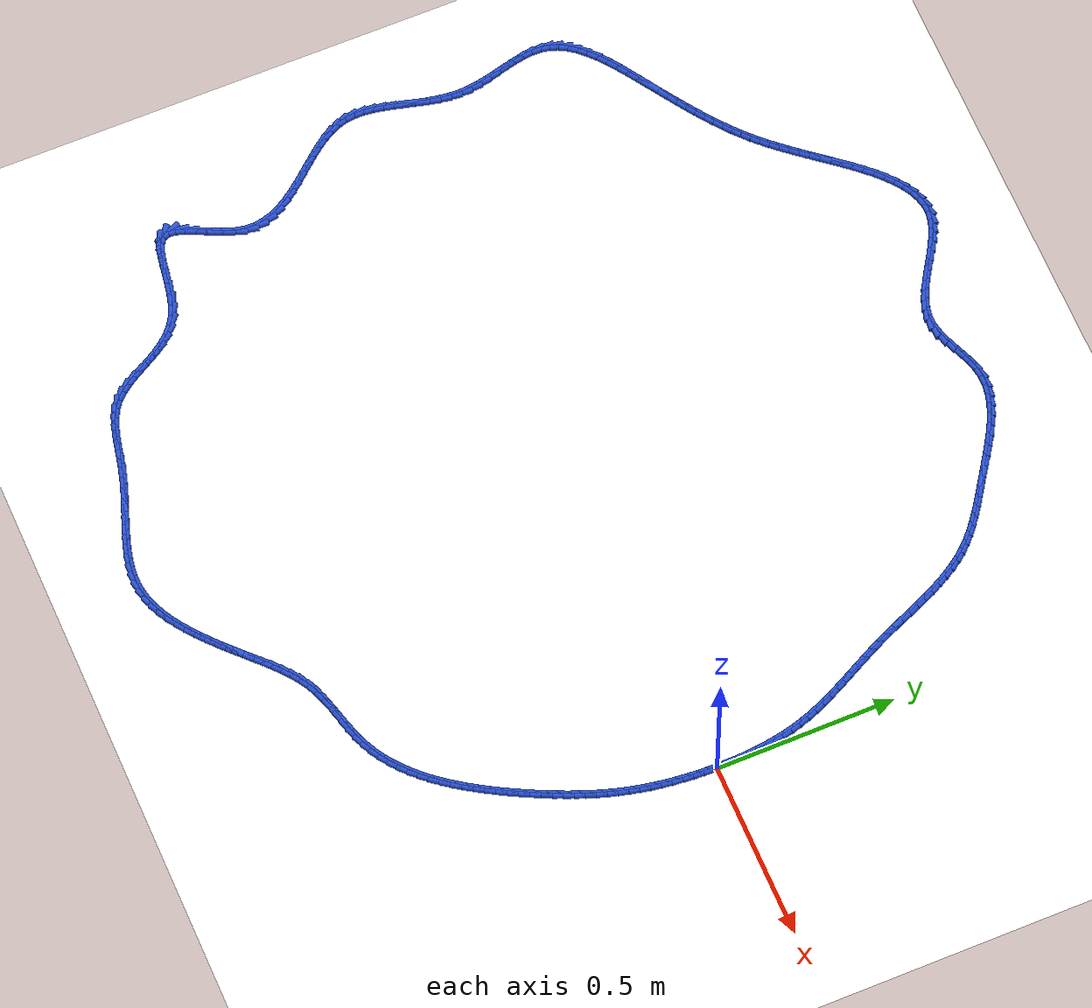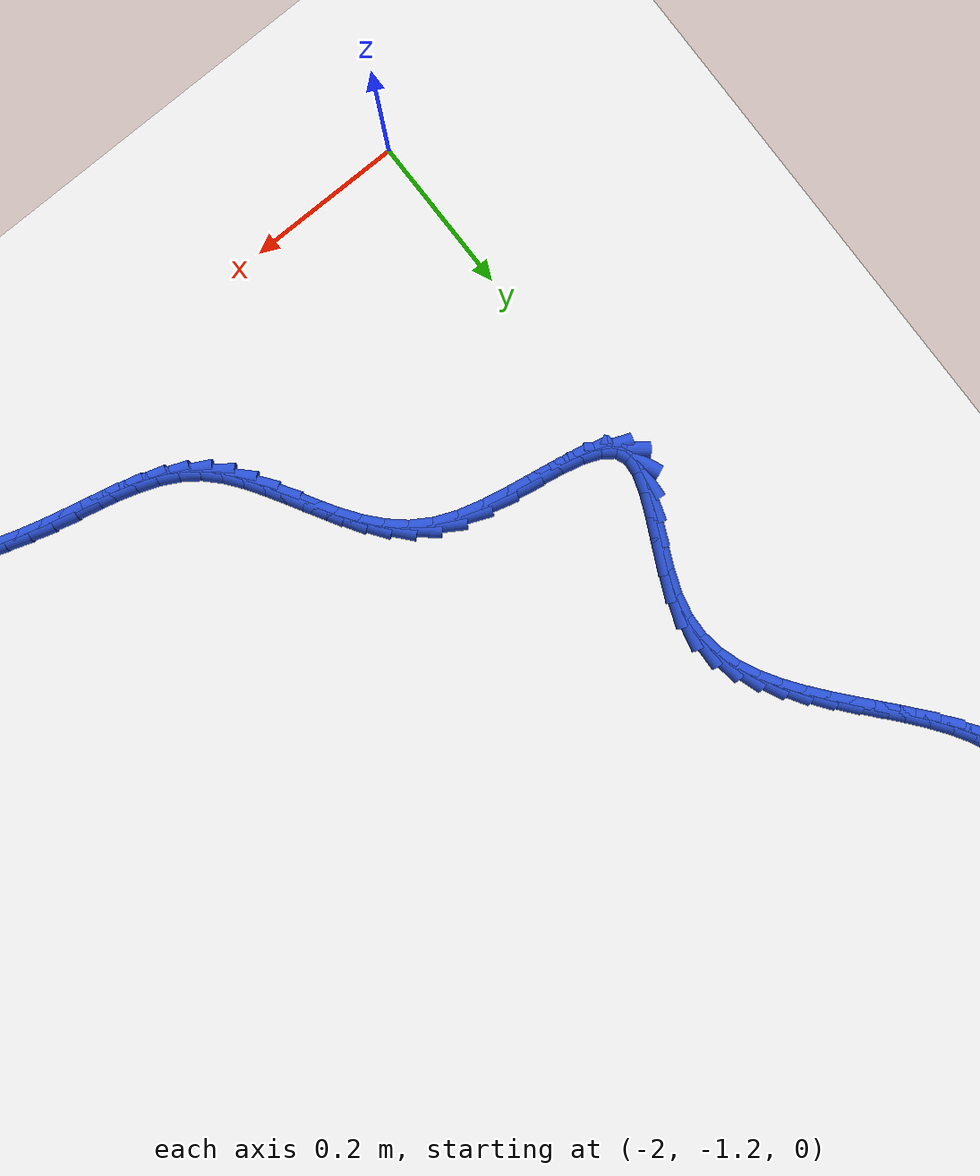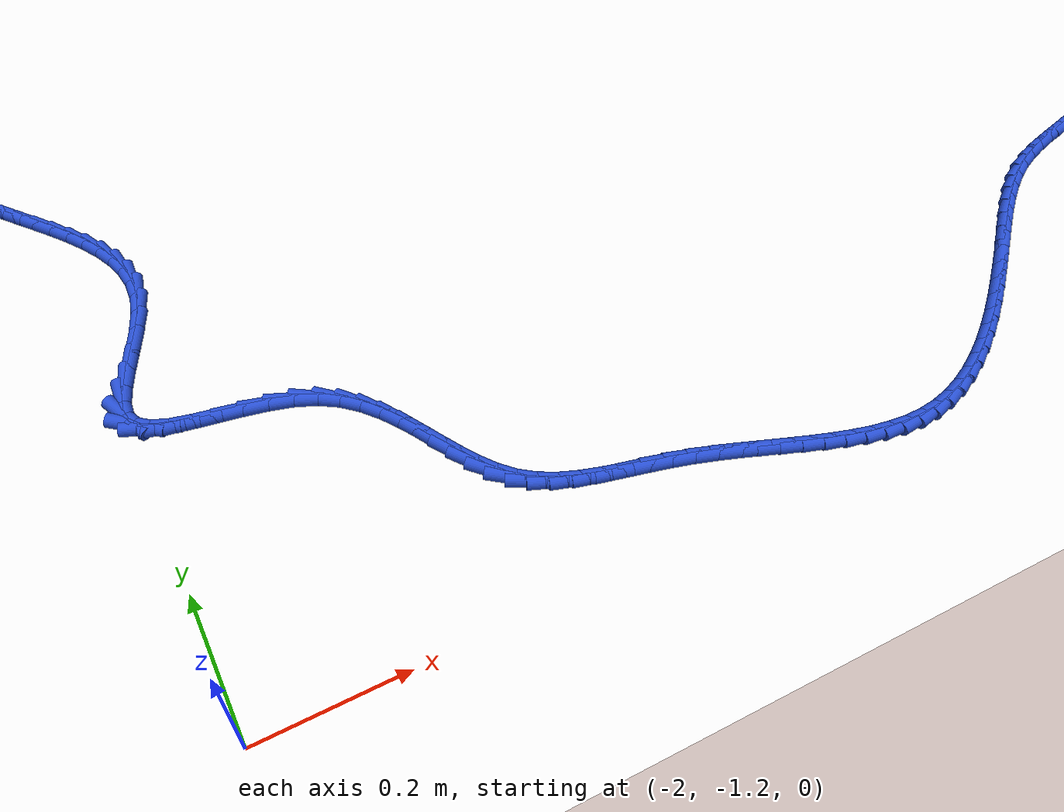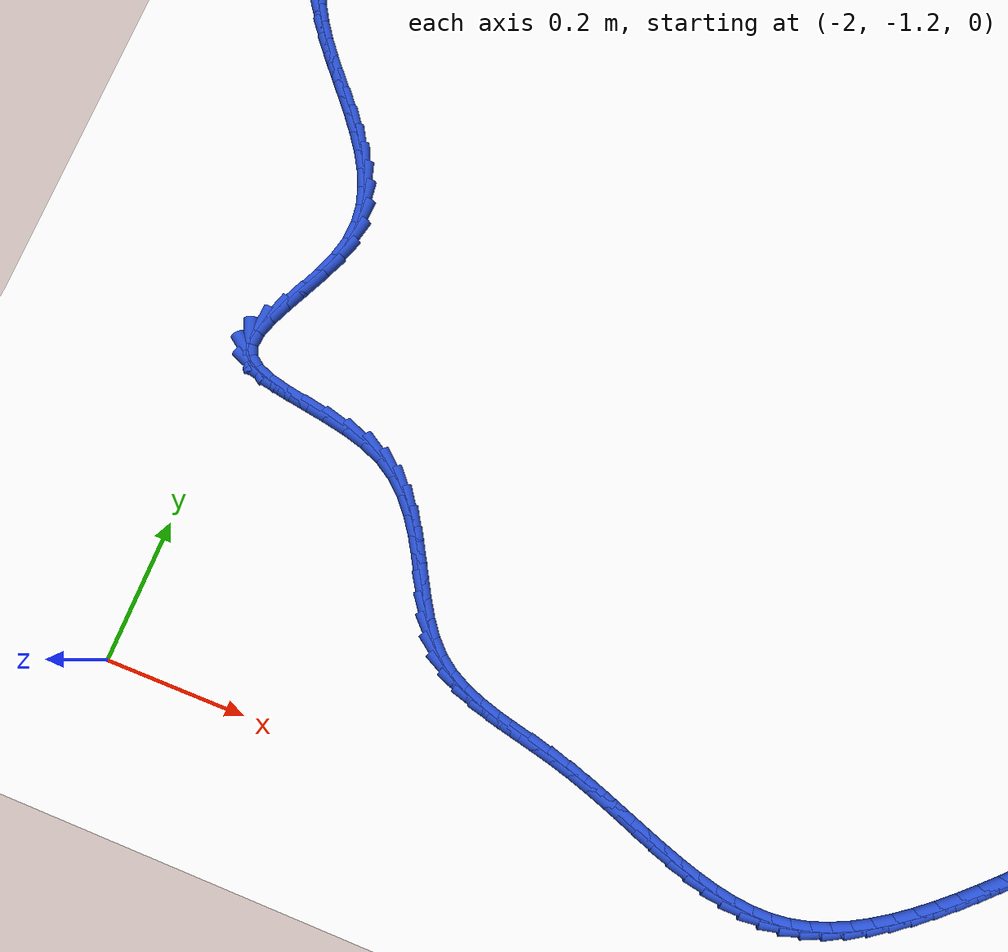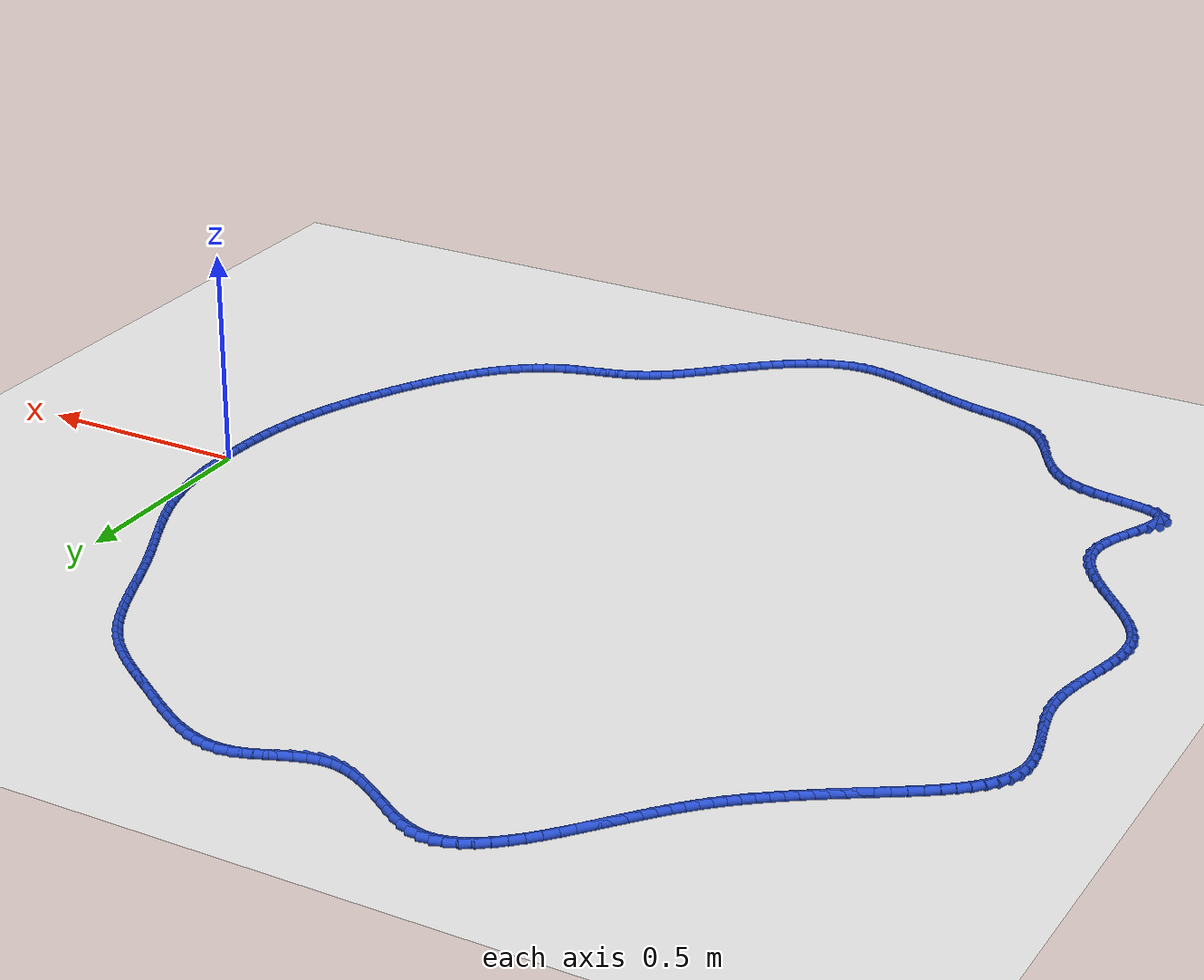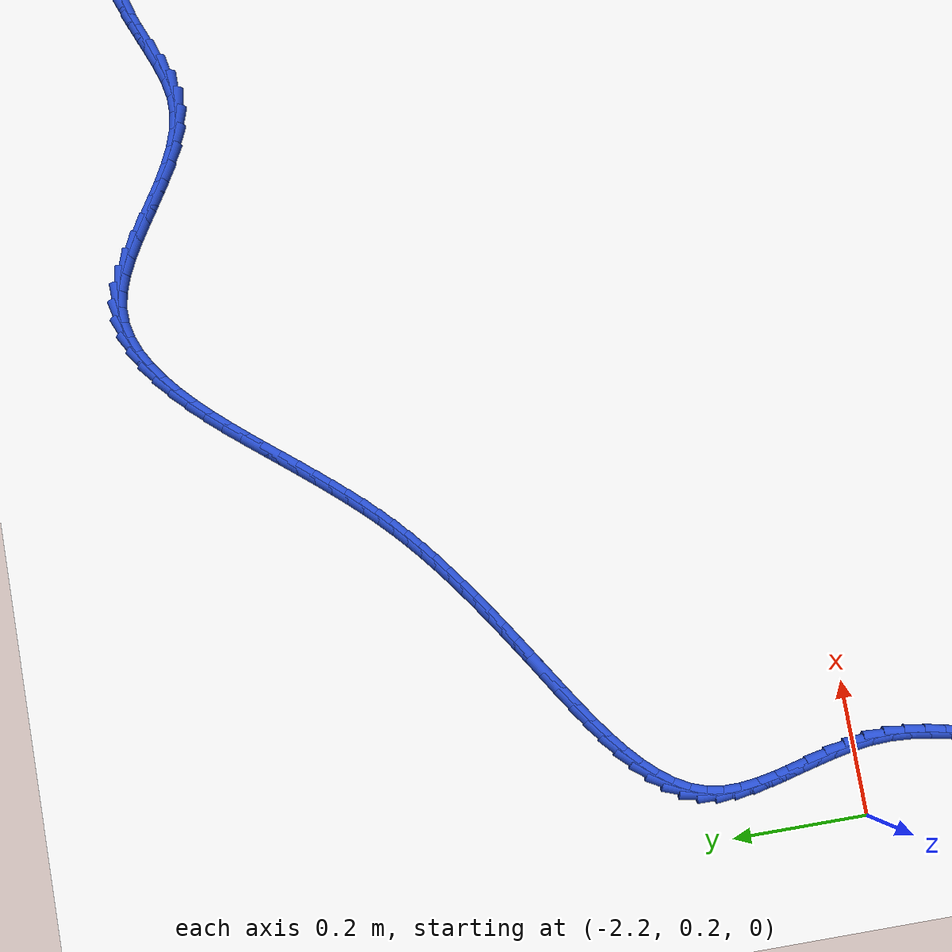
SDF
<sdf version="1.6">
 <world name="default">
  <light name="sun" type="directional">
   <pose>0 0 10 0 -0 0</pose>
   <diffuse>0.8 0.8 0.8 1</diffuse>
   <specular>0.2 0.2 0.2 1</specular>
   <attenuation>
    <range>1000</range>
    <constant>0.9</constant>
    <linear>0.01</linear>
    <quadratic>0.001</quadratic>
   </attenuation>
   <direction>-0.5 0.1 -0.9</direction>
  </light>
  <model name="ground_plane">
   <static>1</static>
   <link name="link">
    <collision name="collision">
     <geometry><plane><normal>0 0 1</normal><size>100 100</size></plane></geometry>
     <surface><friction><ode><mu>100</mu><mu2>50</mu2></ode></friction></surface>
    </collision>
    <visual name="visual">
     <cast_shadows>0</cast_shadows>
     <geometry><plane><normal>0 0 1</normal><size>100 100</size></plane></geometry>
     <material>
      <script><uri>file://media/materials/scripts/gazebo.material</uri><name>Gazebo/WhiteGlow</name></script>
     </material>
    </visual>
   </link>
  </model>
  <gravity>0 0 -9.8</gravity>
  <magnetic_field>6e-06 2.3e-05 -4.2e-05</magnetic_field>
  <atmosphere type="adiabatic"/>
  <physics name="default_physics" default="0" type="ode">
   <max_step_size>0.001</max_step_size>
   <real_time_factor>1</real_time_factor>
   <real_time_update_rate>1000</real_time_update_rate>
  </physics>
  <scene><ambient>0.4 0.4 0.4 1</ambient><background>0.7 0.7 0.7 1</background><shadows>1</shadows></scene>
  <spherical_coordinates>
   <surface_model>EARTH_WGS84</surface_model>
   <latitude_deg>0</latitude_deg>
   <longitude_deg>0</longitude_deg>
   <elevation>0</elevation>
   <heading_deg>0</heading_deg>
  </spherical_coordinates>
  <model name="line">
   <link name="link_0">
    <pose>5.204170427930421e-18 5.551115123125783e-17 0.01 0 1.57 -1.568517945072388</pose>
    <collision name="collision">
     <geometry><cylinder><radius>0.01</radius><length>0.08</length></cylinder></geometry>
    </collision>
    <visual name="visual">
     <material>
      <script><name>Gazebo/Blue</name><uri>file://media/materials/scripts/gazebo.material</uri></script>
     </material>
     <geometry><cylinder><radius>0.01</radius><length>0.08</length></cylinder></geometry>
    </visual>
   </link>
   <link name="link_1">
    <pose>-6.546011237954096e-05 0.028730918293670336 0.01 0 1.57 -1.5427362013400832</pose>
    <collision name="collision">
     <geometry><cylinder><radius>0.01</radius><length>0.08</length></cylinder></geometry>
    </collision>
    <visual name="visual">
     <material>
      <script><name>Gazebo/Blue</name><uri>file://media/materials/scripts/gazebo.material</uri></script>
     </material>
     <geometry><cylinder><radius>0.01</radius><length>0.08</length></cylinder></geometry>
    </visual>
   </link>
   <link name="link_2">
    <pose>-0.0008714124399033945 0.057445714668465736 0.01 0 1.57 -1.5145626425322647</pose>
    <collision name="collision">
     <geometry><cylinder><radius>0.01</radius><length>0.08</length></cylinder></geometry>
    </collision>
    <visual name="visual">
     <material>
      <script><name>Gazebo/Blue</name><uri>file://media/materials/scripts/gazebo.material</uri></script>
     </material>
     <geometry><cylinder><radius>0.01</radius><length>0.08</length></cylinder></geometry>
    </visual>
   </link>
   <link name="link_3">
    <pose>-0.002483616302797522 0.08608520611659495 0.01 0 1.57 -1.4838658375514164</pose>
    <collision name="collision">
     <geometry><cylinder><radius>0.01</radius><length>0.08</length></cylinder></geometry>
    </collision>
    <visual name="visual">
     <material>
      <script><name>Gazebo/Blue</name><uri>file://media/materials/scripts/gazebo.material</uri></script>
     </material>
     <geometry><cylinder><radius>0.01</radius><length>0.08</length></cylinder></geometry>
    </visual>
   </link>
   <link name="link_4">
    <pose>-0.004967831021287884 0.1145902096302667 0.01 0 1.57 -1.450510043880159</pose>
    <collision name="collision">
     <geometry><cylinder><radius>0.01</radius><length>0.08</length></cylinder></geometry>
    </collision>
    <visual name="visual">
     <material>
      <script><name>Gazebo/Blue</name><uri>file://media/materials/scripts/gazebo.material</uri></script>
     </material>
     <geometry><cylinder><radius>0.01</radius><length>0.08</length></cylinder></geometry>
    </visual>
   </link>
   <link name="link_5">
    <pose>-0.008389815915600448 0.14290154220168974 0.01 0 1.57 -1.414360380445874</pose>
    <collision name="collision">
     <geometry><cylinder><radius>0.01</radius><length>0.08</length></cylinder></geometry>
    </collision>
    <visual name="visual">
     <material>
      <script><name>Gazebo/Blue</name><uri>file://media/materials/scripts/gazebo.material</uri></script>
     </material>
     <geometry><cylinder><radius>0.01</radius><length>0.08</length></cylinder></geometry>
    </visual>
   </link>
   <link name="link_6">
    <pose>-0.01281533030596118 0.17096002082307274 0.01 0 1.57 -1.3752896316140557</pose>
    <collision name="collision">
     <geometry><cylinder><radius>0.01</radius><length>0.08</length></cylinder></geometry>
    </collision>
    <visual name="visual">
     <material>
      <script><name>Gazebo/Blue</name><uri>file://media/materials/scripts/gazebo.material</uri></script>
     </material>
     <geometry><cylinder><radius>0.01</radius><length>0.08</length></cylinder></geometry>
    </visual>
   </link>
   <link name="link_7">
    <pose>-0.018310133512596034 0.19870646248662432 0.01 0 1.57 -1.3331869514808536</pose>
    <collision name="collision">
     <geometry><cylinder><radius>0.01</radius><length>0.08</length></cylinder></geometry>
    </collision>
    <visual name="visual">
     <material>
      <script><name>Gazebo/Blue</name><uri>file://media/materials/scripts/gazebo.material</uri></script>
     </material>
     <geometry><cylinder><radius>0.01</radius><length>0.08</length></cylinder></geometry>
    </visual>
   </link>
   <link name="link_8">
    <pose>-0.02493998485573099 0.22608168418455338 0.01 0 1.57 -1.2879750825685923</pose>
    <collision name="collision">
     <geometry><cylinder><radius>0.01</radius><length>0.08</length></cylinder></geometry>
    </collision>
    <visual name="visual">
     <material>
      <script><name>Gazebo/Blue</name><uri>file://media/materials/scripts/gazebo.material</uri></script>
     </material>
     <geometry><cylinder><radius>0.01</radius><length>0.08</length></cylinder></geometry>
    </visual>
   </link>
   <link name="link_9">
    <pose>-0.03277048302589974 0.2530266002973392 0.01 0 1.57 -1.2419998102372325</pose>
    <collision name="collision">
     <geometry><cylinder><radius>0.01</radius><length>0.08</length></cylinder></geometry>
    </collision>
    <visual name="visual">
     <material>
      <script><name>Gazebo/Blue</name><uri>file://media/materials/scripts/gazebo.material</uri></script>
     </material>
     <geometry><cylinder><radius>0.01</radius><length>0.08</length></cylinder></geometry>
    </visual>
   </link>
   <link name="link_10">
    <pose>-0.04180870425800232 0.27951760681951265 0.01 0 1.57 -1.2013344754317694</pose>
    <collision name="collision">
     <geometry><cylinder><radius>0.01</radius><length>0.08</length></cylinder></geometry>
    </collision>
    <visual name="visual">
     <material>
      <script><name>Gazebo/Blue</name><uri>file://media/materials/scripts/gazebo.material</uri></script>
     </material>
     <geometry><cylinder><radius>0.01</radius><length>0.08</length></cylinder></geometry>
    </visual>
   </link>
   <link name="link_11">
    <pose>-0.051916398236841216 0.30561920986515134 0.01 0 1.57 -1.1670903041491385</pose>
    <collision name="collision">
     <geometry><cylinder><radius>0.01</radius><length>0.08</length></cylinder></geometry>
    </collision>
    <visual name="visual">
     <material>
      <script><name>Gazebo/Blue</name><uri>file://media/materials/scripts/gazebo.material</uri></script>
     </material>
     <geometry><cylinder><radius>0.01</radius><length>0.08</length></cylinder></geometry>
    </visual>
   </link>
   <link name="link_12">
    <pose>-0.06293314005880227 0.3314093597925878 0.01 0 1.57 -1.1393570549071346</pose>
    <collision name="collision">
     <geometry><cylinder><radius>0.01</radius><length>0.08</length></cylinder></geometry>
    </collision>
    <visual name="visual">
     <material>
      <script><name>Gazebo/Blue</name><uri>file://media/materials/scripts/gazebo.material</uri></script>
     </material>
     <geometry><cylinder><radius>0.01</radius><length>0.08</length></cylinder></geometry>
    </visual>
   </link>
   <link name="link_13">
    <pose>-0.0746985048202713 0.3569660069601546 0.01 0 1.57 -1.118136493532173</pose>
    <collision name="collision">
     <geometry><cylinder><radius>0.01</radius><length>0.08</length></cylinder></geometry>
    </collision>
    <visual name="visual">
     <material>
      <script><name>Gazebo/Blue</name><uri>file://media/materials/scripts/gazebo.material</uri></script>
     </material>
     <geometry><cylinder><radius>0.01</radius><length>0.08</length></cylinder></geometry>
    </visual>
   </link>
   <link name="link_14">
    <pose>-0.08705206761763412 0.38236710172618454 0.01 0 1.57 -1.1033778785597421</pose>
    <collision name="collision">
     <geometry><cylinder><radius>0.01</radius><length>0.08</length></cylinder></geometry>
    </collision>
    <visual name="visual">
     <material>
      <script><name>Gazebo/Blue</name><uri>file://media/materials/scripts/gazebo.material</uri></script>
     </material>
     <geometry><cylinder><radius>0.01</radius><length>0.08</length></cylinder></geometry>
    </visual>
   </link>
   <link name="link_15">
    <pose>-0.0998334035472766 0.40769059444901 0.01 0 1.57 -1.0950053365914658</pose>
    <collision name="collision">
     <geometry><cylinder><radius>0.01</radius><length>0.08</length></cylinder></geometry>
    </collision>
    <visual name="visual">
     <material>
      <script><name>Gazebo/Blue</name><uri>file://media/materials/scripts/gazebo.material</uri></script>
     </material>
     <geometry><cylinder><radius>0.01</radius><length>0.08</length></cylinder></geometry>
    </visual>
   </link>
   <link name="link_16">
    <pose>-0.1128820877055846 0.43301443548696383 0.01 0 1.57 -1.0929364655374936</pose>
    <collision name="collision">
     <geometry><cylinder><radius>0.01</radius><length>0.08</length></cylinder></geometry>
    </collision>
    <visual name="visual">
     <material>
      <script><name>Gazebo/Blue</name><uri>file://media/materials/scripts/gazebo.material</uri></script>
     </material>
     <geometry><cylinder><radius>0.01</radius><length>0.08</length></cylinder></geometry>
    </visual>
   </link>
   <link name="link_17">
    <pose>-0.12603769518894398 0.4584165751983787 0.01 0 1.57 -1.097092465461059</pose>
    <collision name="collision">
     <geometry><cylinder><radius>0.01</radius><length>0.08</length></cylinder></geometry>
    </collision>
    <visual name="visual">
     <material>
      <script><name>Gazebo/Blue</name><uri>file://media/materials/scripts/gazebo.material</uri></script>
     </material>
     <geometry><cylinder><radius>0.01</radius><length>0.08</length></cylinder></geometry>
    </visual>
   </link>
   <link name="link_18">
    <pose>-0.13913980109374052 0.483974963941587 0.01 0 1.57 -1.107400438641858</pose>
    <collision name="collision">
     <geometry><cylinder><radius>0.01</radius><length>0.08</length></cylinder></geometry>
    </collision>
    <visual name="visual">
     <material>
      <script><name>Gazebo/Blue</name><uri>file://media/materials/scripts/gazebo.material</uri></script>
     </material>
     <geometry><cylinder><radius>0.01</radius><length>0.08</length></cylinder></geometry>
    </visual>
   </link>
   <link name="link_19">
    <pose>-0.15202798051636007 0.5097675520749214 0.01 0 1.57 -1.1237885111083326</pose>
    <collision name="collision">
     <geometry><cylinder><radius>0.01</radius><length>0.08</length></cylinder></geometry>
    </collision>
    <visual name="visual">
     <material>
      <script><name>Gazebo/Blue</name><uri>file://media/materials/scripts/gazebo.material</uri></script>
     </material>
     <geometry><cylinder><radius>0.01</radius><length>0.08</length></cylinder></geometry>
    </visual>
   </link>
   <link name="link_20">
    <pose>-0.1645418085531885 0.5358722899567145 0.01 0 1.57 -1.1443840696282837</pose>
    <collision name="collision">
     <geometry><cylinder><radius>0.01</radius><length>0.08</length></cylinder></geometry>
    </collision>
    <visual name="visual">
     <material>
      <script><name>Gazebo/Blue</name><uri>file://media/materials/scripts/gazebo.material</uri></script>
     </material>
     <geometry><cylinder><radius>0.01</radius><length>0.08</length></cylinder></geometry>
    </visual>
   </link>
   <link name="link_21">
    <pose>-0.17656451619382074 0.5623373662047823 0.01 0 1.57 -1.1601407667916381</pose>
    <collision name="collision">
     <geometry><cylinder><radius>0.01</radius><length>0.08</length></cylinder></geometry>
    </collision>
    <visual name="visual">
     <material>
      <script><name>Gazebo/Blue</name><uri>file://media/materials/scripts/gazebo.material</uri></script>
     </material>
     <geometry><cylinder><radius>0.01</radius><length>0.08</length></cylinder></geometry>
    </visual>
   </link>
   <link name="link_22">
    <pose>-0.18820005609602605 0.589060495800236 0.01 0 1.57 -1.1683401843044885</pose>
    <collision name="collision">
     <geometry><cylinder><radius>0.01</radius><length>0.08</length></cylinder></geometry>
    </collision>
    <visual name="visual">
     <material>
      <script><name>Gazebo/Blue</name><uri>file://media/materials/scripts/gazebo.material</uri></script>
     </material>
     <geometry><cylinder><radius>0.01</radius><length>0.08</length></cylinder></geometry>
    </visual>
   </link>
   <link name="link_23">
    <pose>-0.19962197544693255 0.615891948713402 0.01 0 1.57 -1.1690486684555863</pose>
    <collision name="collision">
     <geometry><cylinder><radius>0.01</radius><length>0.08</length></cylinder></geometry>
    </collision>
    <visual name="visual">
     <material>
      <script><name>Gazebo/Blue</name><uri>file://media/materials/scripts/gazebo.material</uri></script>
     </material>
     <geometry><cylinder><radius>0.01</radius><length>0.08</length></cylinder></geometry>
    </visual>
   </link>
   <link name="link_24">
    <pose>-0.211003847665836 0.6426819770312251 0.01 0 1.57 -1.1622295150099458</pose>
    <collision name="collision">
     <geometry><cylinder><radius>0.01</radius><length>0.08</length></cylinder></geometry>
    </collision>
    <visual name="visual">
     <material>
      <script><name>Gazebo/Blue</name><uri>file://media/materials/scripts/gazebo.material</uri></script>
     </material>
     <geometry><cylinder><radius>0.01</radius><length>0.08</length></cylinder></geometry>
    </visual>
   </link>
   <link name="link_25">
    <pose>-0.22251924617203203 0.6692808328406501 0.01 0 1.57 -1.1477388641497936</pose>
    <collision name="collision">
     <geometry><cylinder><radius>0.01</radius><length>0.08</length></cylinder></geometry>
    </collision>
    <visual name="visual">
     <material>
      <script><name>Gazebo/Blue</name><uri>file://media/materials/scripts/gazebo.material</uri></script>
     </material>
     <geometry><cylinder><radius>0.01</radius><length>0.08</length></cylinder></geometry>
    </visual>
   </link>
   <link name="link_26">
    <pose>-0.23434174438481659 0.6955387682286218 0.01 0 1.57 -1.1253322727199992</pose>
    <collision name="collision">
     <geometry><cylinder><radius>0.01</radius><length>0.08</length></cylinder></geometry>
    </collision>
    <visual name="visual">
     <material>
      <script><name>Gazebo/Blue</name><uri>file://media/materials/scripts/gazebo.material</uri></script>
     </material>
     <geometry><cylinder><radius>0.01</radius><length>0.08</length></cylinder></geometry>
    </visual>
   </link>
   <link name="link_27">
    <pose>-0.24664491572348524 0.7213060352820849 0.01 0 1.57 -1.0946834402532364</pose>
    <collision name="collision">
     <geometry><cylinder><radius>0.01</radius><length>0.08</length></cylinder></geometry>
    </collision>
    <visual name="visual">
     <material>
      <script><name>Gazebo/Blue</name><uri>file://media/materials/scripts/gazebo.material</uri></script>
     </material>
     <geometry><cylinder><radius>0.01</radius><length>0.08</length></cylinder></geometry>
    </visual>
   </link>
   <link name="link_28">
    <pose>-0.25960233360733403 0.7464328860879847 0.01 0 1.57 -1.0554199955556023</pose>
    <collision name="collision">
     <geometry><cylinder><radius>0.01</radius><length>0.08</length></cylinder></geometry>
    </collision>
    <visual name="visual">
     <material>
      <script><name>Gazebo/Blue</name><uri>file://media/materials/scripts/gazebo.material</uri></script>
     </material>
     <geometry><cylinder><radius>0.01</radius><length>0.08</length></cylinder></geometry>
    </visual>
   </link>
   <link name="link_29">
    <pose>-0.27338757145565856 0.7707695727332661 0.01 0 1.57 -1.0071831119404284</pose>
    <collision name="collision">
     <geometry><cylinder><radius>0.01</radius><length>0.08</length></cylinder></geometry>
    </collision>
    <visual name="visual">
     <material>
      <script><name>Gazebo/Blue</name><uri>file://media/materials/scripts/gazebo.material</uri></script>
     </material>
     <geometry><cylinder><radius>0.01</radius><length>0.08</length></cylinder></geometry>
    </visual>
   </link>
   <link name="link_30">
    <pose>-0.2881742026877546 0.7941663473048736 0.01 0 1.57 -0.9497178227277111</pose>
    <collision name="collision">
     <geometry><cylinder><radius>0.01</radius><length>0.08</length></cylinder></geometry>
    </collision>
    <visual name="visual">
     <material>
      <script><name>Gazebo/Blue</name><uri>file://media/materials/scripts/gazebo.material</uri></script>
     </material>
     <geometry><cylinder><radius>0.01</radius><length>0.08</length></cylinder></geometry>
    </visual>
   </link>
   <link name="link_31">
    <pose>-0.304135800722918 0.816473461889752 0.01 0 1.57 -0.8830179331825097</pose>
    <collision name="collision">
     <geometry><cylinder><radius>0.01</radius><length>0.08</length></cylinder></geometry>
    </collision>
    <visual name="visual">
     <material>
      <script><name>Gazebo/Blue</name><uri>file://media/materials/scripts/gazebo.material</uri></script>
     </material>
     <geometry><cylinder><radius>0.01</radius><length>0.08</length></cylinder></geometry>
    </visual>
   </link>
   <link name="link_32">
    <pose>-0.3214455577959444 0.837541607221992 0.01 0 1.57 -0.8123300044781248</pose>
    <collision name="collision">
     <geometry><cylinder><radius>0.01</radius><length>0.08</length></cylinder></geometry>
    </collision>
    <visual name="visual">
     <material>
      <script><name>Gazebo/Blue</name><uri>file://media/materials/scripts/gazebo.material</uri></script>
     </material>
     <geometry><cylinder><radius>0.01</radius><length>0.08</length></cylinder></geometry>
    </visual>
   </link>
   <link name="link_33">
    <pose>-0.3401887800847428 0.8573226087040168 0.01 0 1.57 -0.7496124533951917</pose>
    <collision name="collision">
     <geometry><cylinder><radius>0.01</radius><length>0.08</length></cylinder></geometry>
    </collision>
    <visual name="visual">
     <material>
      <script><name>Gazebo/Blue</name><uri>file://media/materials/scripts/gazebo.material</uri></script>
     </material>
     <geometry><cylinder><radius>0.01</radius><length>0.08</length></cylinder></geometry>
    </visual>
   </link>
   <link name="link_34">
    <pose>-0.3602510944996789 0.875998072174546 0.01 0 1.57 -0.6970603639408066</pose>
    <collision name="collision">
     <geometry><cylinder><radius>0.01</radius><length>0.08</length></cylinder></geometry>
    </collision>
    <visual name="visual">
     <material>
      <script><name>Gazebo/Blue</name><uri>file://media/materials/scripts/gazebo.material</uri></script>
     </material>
     <geometry><cylinder><radius>0.01</radius><length>0.08</length></cylinder></geometry>
    </visual>
   </link>
   <link name="link_35">
    <pose>-0.38149054413228434 0.8937813454854017 0.01 0 1.57 -0.6548518049781613</pose>
    <collision name="collision">
     <geometry><cylinder><radius>0.01</radius><length>0.08</length></cylinder></geometry>
    </collision>
    <visual name="visual">
     <material>
      <script><name>Gazebo/Blue</name><uri>file://media/materials/scripts/gazebo.material</uri></script>
     </material>
     <geometry><cylinder><radius>0.01</radius><length>0.08</length></cylinder></geometry>
    </visual>
   </link>
   <link name="link_36">
    <pose>-0.4037651720740903 0.910885776488405 0.01 0 1.57 -0.6228305214378709</pose>
    <collision name="collision">
     <geometry><cylinder><radius>0.01</radius><length>0.08</length></cylinder></geometry>
    </collision>
    <visual name="visual">
     <material>
      <script><name>Gazebo/Blue</name><uri>file://media/materials/scripts/gazebo.material</uri></script>
     </material>
     <geometry><cylinder><radius>0.01</radius><length>0.08</length></cylinder></geometry>
    </visual>
   </link>
   <link name="link_37">
    <pose>-0.42693302141662837 0.9275247130353775 0.01 0 1.57 -0.6006502645675779</pose>
    <collision name="collision">
     <geometry><cylinder><radius>0.01</radius><length>0.08</length></cylinder></geometry>
    </collision>
    <visual name="visual">
     <material>
      <script><name>Gazebo/Blue</name><uri>file://media/materials/scripts/gazebo.material</uri></script>
     </material>
     <geometry><cylinder><radius>0.01</radius><length>0.08</length></cylinder></geometry>
    </visual>
   </link>
   <link name="link_38">
    <pose>-0.45085213525143025 0.9439115029781415 0.01 0 1.57 -0.5878815166539876</pose>
    <collision name="collision">
     <geometry><cylinder><radius>0.01</radius><length>0.08</length></cylinder></geometry>
    </collision>
    <visual name="visual">
     <material>
      <script><name>Gazebo/Blue</name><uri>file://media/materials/scripts/gazebo.material</uri></script>
     </material>
     <geometry><cylinder><radius>0.01</radius><length>0.08</length></cylinder></geometry>
    </visual>
   </link>
   <link name="link_39">
    <pose>-0.4753805566700272 0.9602594941685182 0.01 0 1.57 -0.5840785848746476</pose>
    <collision name="collision">
     <geometry><cylinder><radius>0.01</radius><length>0.08</length></cylinder></geometry>
    </collision>
    <visual name="visual">
     <material>
      <script><name>Gazebo/Blue</name><uri>file://media/materials/scripts/gazebo.material</uri></script>
     </material>
     <geometry><cylinder><radius>0.01</radius><length>0.08</length></cylinder></geometry>
    </visual>
   </link>
   <link name="link_40">
    <pose>-0.500376328763951 0.9767820344583298 0.01 0 1.57 -0.587453980085998</pose>
    <collision name="collision">
     <geometry><cylinder><radius>0.01</radius><length>0.08</length></cylinder></geometry>
    </collision>
    <visual name="visual">
     <material>
      <script><name>Gazebo/Blue</name><uri>file://media/materials/scripts/gazebo.material</uri></script>
     </material>
     <geometry><cylinder><radius>0.01</radius><length>0.08</length></cylinder></geometry>
    </visual>
   </link>
   <link name="link_41">
    <pose>-0.5257052904424686 0.9936479441568535 0.01 0 1.57 -0.5851930315225743</pose>
    <collision name="collision">
     <geometry><cylinder><radius>0.01</radius><length>0.08</length></cylinder></geometry>
    </collision>
    <visual name="visual">
     <material>
      <script><name>Gazebo/Blue</name><uri>file://media/materials/scripts/gazebo.material</uri></script>
     </material>
     <geometry><cylinder><radius>0.01</radius><length>0.08</length></cylinder></geometry>
    </visual>
   </link>
   <link name="link_42">
    <pose>-0.5513058913543827 1.0106113112254147 0.01 0 1.57 -0.5705512847842199</pose>
    <collision name="collision">
     <geometry><cylinder><radius>0.01</radius><length>0.08</length></cylinder></geometry>
    </collision>
    <visual name="visual">
     <material>
      <script><name>Gazebo/Blue</name><uri>file://media/materials/scripts/gazebo.material</uri></script>
     </material>
     <geometry><cylinder><radius>0.01</radius><length>0.08</length></cylinder></geometry>
    </visual>
   </link>
   <link name="link_43">
    <pose>-0.5771560855449007 1.0272005855010071 0.01 0 1.57 -0.5430795092193399</pose>
    <collision name="collision">
     <geometry><cylinder><radius>0.01</radius><length>0.08</length></cylinder></geometry>
    </collision>
    <visual name="visual">
     <material>
      <script><name>Gazebo/Blue</name><uri>file://media/materials/scripts/gazebo.material</uri></script>
     </material>
     <geometry><cylinder><radius>0.01</radius><length>0.08</length></cylinder></geometry>
    </visual>
   </link>
   <link name="link_44">
    <pose>-0.6032342223228504 1.042941959184755 0.01 0 1.57 -0.5017685302095107</pose>
    <collision name="collision">
     <geometry><cylinder><radius>0.01</radius><length>0.08</length></cylinder></geometry>
    </collision>
    <visual name="visual">
     <material>
      <script><name>Gazebo/Blue</name><uri>file://media/materials/scripts/gazebo.material</uri></script>
     </material>
     <geometry><cylinder><radius>0.01</radius><length>0.08</length></cylinder></geometry>
    </visual>
   </link>
   <link name="link_45">
    <pose>-0.6295186509970614 1.0573616244777857 0.01 0 1.57 -0.4450297321661276</pose>
    <collision name="collision">
     <geometry><cylinder><radius>0.01</radius><length>0.08</length></cylinder></geometry>
    </collision>
    <visual name="visual">
     <material>
      <script><name>Gazebo/Blue</name><uri>file://media/materials/scripts/gazebo.material</uri></script>
     </material>
     <geometry><cylinder><radius>0.01</radius><length>0.08</length></cylinder></geometry>
    </visual>
   </link>
   <link name="link_46">
    <pose>-0.655987720876362 1.0699857735812242 0.01 0 1.57 -0.37082320882095143</pose>
    <collision name="collision">
     <geometry><cylinder><radius>0.01</radius><length>0.08</length></cylinder></geometry>
    </collision>
    <visual name="visual">
     <material>
      <script><name>Gazebo/Blue</name><uri>file://media/materials/scripts/gazebo.material</uri></script>
     </material>
     <geometry><cylinder><radius>0.01</radius><length>0.08</length></cylinder></geometry>
    </visual>
   </link>
   <link name="link_47">
    <pose>-0.6826197812695807 1.0803405986961965 0.01 0 1.57 -0.27699216461119053</pose>
    <collision name="collision">
     <geometry><cylinder><radius>0.01</radius><length>0.08</length></cylinder></geometry>
    </collision>
    <visual name="visual">
     <material>
      <script><name>Gazebo/Blue</name><uri>file://media/materials/scripts/gazebo.material</uri></script>
     </material>
     <geometry><cylinder><radius>0.01</radius><length>0.08</length></cylinder></geometry>
    </visual>
   </link>
   <link name="link_48">
    <pose>-0.7093931814855465 1.0879522920238285 0.01 0 1.57 -0.16198394295709873</pose>
    <collision name="collision">
     <geometry><cylinder><radius>0.01</radius><length>0.08</length></cylinder></geometry>
    </collision>
    <visual name="visual">
     <material>
      <script><name>Gazebo/Blue</name><uri>file://media/materials/scripts/gazebo.material</uri></script>
     </material>
     <geometry><cylinder><radius>0.01</radius><length>0.08</length></cylinder></geometry>
    </visual>
   </link>
   <link name="link_49">
    <pose>-0.7362862708330875 1.0923470457652456 0.01 0 1.57 -0.026076967880432046</pose>
    <collision name="collision">
     <geometry><cylinder><radius>0.01</radius><length>0.08</length></cylinder></geometry>
    </collision>
    <visual name="visual">
     <material>
      <script><name>Gazebo/Blue</name><uri>file://media/materials/scripts/gazebo.material</uri></script>
     </material>
     <geometry><cylinder><radius>0.01</radius><length>0.08</length></cylinder></geometry>
    </visual>
   </link>
   <link name="link_50">
    <pose>-0.763277398621033 1.0930510521215742 0.01 0 1.57 0.126999701816529</pose>
    <collision name="collision">
     <geometry><cylinder><radius>0.01</radius><length>0.08</length></cylinder></geometry>
    </collision>
    <visual name="visual">
     <material>
      <script><name>Gazebo/Blue</name><uri>file://media/materials/scripts/gazebo.material</uri></script>
     </material>
     <geometry><cylinder><radius>0.01</radius><length>0.08</length></cylinder></geometry>
    </visual>
   </link>
   <link name="link_51">
    <pose>-0.7903449107371074 1.0895948847225505 0.01 0 1.57 0.26878209734586767</pose>
    <collision name="collision">
     <geometry><cylinder><radius>0.01</radius><length>0.08</length></cylinder></geometry>
    </collision>
    <visual name="visual">
     <material>
      <script><name>Gazebo/Blue</name><uri>file://media/materials/scripts/gazebo.material</uri></script>
     </material>
     <geometry><cylinder><radius>0.01</radius><length>0.08</length></cylinder></geometry>
    </visual>
   </link>
   <link name="link_52">
    <pose>-0.8174666727488402 1.0821242661901158 0.01 0 1.57 0.35597840947852405</pose>
    <collision name="collision">
     <geometry><cylinder><radius>0.01</radius><length>0.08</length></cylinder></geometry>
    </collision>
    <visual name="visual">
     <material>
      <script><name>Gazebo/Blue</name><uri>file://media/materials/scripts/gazebo.material</uri></script>
     </material>
     <geometry><cylinder><radius>0.01</radius><length>0.08</length></cylinder></geometry>
    </visual>
   </link>
   <link name="link_53">
    <pose>-0.8446195793556127 1.0720283158809307 0.01 0 1.57 0.39055654548071</pose>
    <collision name="collision">
     <geometry><cylinder><radius>0.01</radius><length>0.08</length></cylinder></geometry>
    </collision>
    <visual name="visual">
     <material>
      <script><name>Gazebo/Blue</name><uri>file://media/materials/scripts/gazebo.material</uri></script>
     </material>
     <geometry><cylinder><radius>0.01</radius><length>0.08</length></cylinder></geometry>
    </visual>
   </link>
   <link name="link_54">
    <pose>-0.8717804082150313 1.0608460492646994 0.01 0 1.57 0.3764143237835546</pose>
    <collision name="collision">
     <geometry><cylinder><radius>0.01</radius><length>0.08</length></cylinder></geometry>
    </collision>
    <visual name="visual">
     <material>
      <script><name>Gazebo/Blue</name><uri>file://media/materials/scripts/gazebo.material</uri></script>
     </material>
     <geometry><cylinder><radius>0.01</radius><length>0.08</length></cylinder></geometry>
    </visual>
   </link>
   <link name="link_55">
    <pose>-0.8989259369847026 1.050116481811126 0.01 0 1.57 0.3118301706937674</pose>
    <collision name="collision">
     <geometry><cylinder><radius>0.01</radius><length>0.08</length></cylinder></geometry>
    </collision>
    <visual name="visual">
     <material>
      <script><name>Gazebo/Blue</name><uri>file://media/materials/scripts/gazebo.material</uri></script>
     </material>
     <geometry><cylinder><radius>0.01</radius><length>0.08</length></cylinder></geometry>
    </visual>
   </link>
   <link name="link_56">
    <pose>-0.926032943322232 1.0413786289899145 0.01 0 1.57 0.1902061707704024</pose>
    <collision name="collision">
     <geometry><cylinder><radius>0.01</radius><length>0.08</length></cylinder></geometry>
    </collision>
    <visual name="visual">
     <material>
      <script><name>Gazebo/Blue</name><uri>file://media/materials/scripts/gazebo.material</uri></script>
     </material>
     <geometry><cylinder><radius>0.01</radius><length>0.08</length></cylinder></geometry>
    </visual>
   </link>
   <link name="link_57">
    <pose>-0.9530782048852259 1.036171506270769 0.01 0 1.57 0.008145959631315234</pose>
    <collision name="collision">
     <geometry><cylinder><radius>0.01</radius><length>0.08</length></cylinder></geometry>
    </collision>
    <visual name="visual">
     <material>
      <script><name>Gazebo/Blue</name><uri>file://media/materials/scripts/gazebo.material</uri></script>
     </material>
     <geometry><cylinder><radius>0.01</radius><length>0.08</length></cylinder></geometry>
    </visual>
   </link>
   <link name="link_58">
    <pose>-0.9800387461718391 1.0359518819319427 0.01 0 1.57 -0.1807595156623004</pose>
    <collision name="collision">
     <geometry><cylinder><radius>0.01</radius><length>0.08</length></cylinder></geometry>
    </collision>
    <visual name="visual">
     <material>
      <script><name>Gazebo/Blue</name><uri>file://media/materials/scripts/gazebo.material</uri></script>
     </material>
     <geometry><cylinder><radius>0.01</radius><length>0.08</length></cylinder></geometry>
    </visual>
   </link>
   <link name="link_59">
    <pose>-1.0068955426060162 1.0408600770474845 0.01 0 1.57 -0.32862777557520384</pose>
    <collision name="collision">
     <geometry><cylinder><radius>0.01</radius><length>0.08</length></cylinder></geometry>
    </collision>
    <visual name="visual">
     <material>
      <script><name>Gazebo/Blue</name><uri>file://media/materials/scripts/gazebo.material</uri></script>
     </material>
     <geometry><cylinder><radius>0.01</radius><length>0.08</length></cylinder></geometry>
    </visual>
   </link>
   <link name="link_60">
    <pose>-1.0336327483438492 1.0499772601610495 0.01 0 1.57 -0.43548794238833743</pose>
    <collision name="collision">
     <geometry><cylinder><radius>0.01</radius><length>0.08</length></cylinder></geometry>
    </collision>
    <visual name="visual">
     <material>
      <script><name>Gazebo/Blue</name><uri>file://media/materials/scripts/gazebo.material</uri></script>
     </material>
     <geometry><cylinder><radius>0.01</radius><length>0.08</length></cylinder></geometry>
    </visual>
   </link>
   <link name="link_61">
    <pose>-1.0602346076500864 1.062354575641385 0.01 0 1.57 -0.5069172658871428</pose>
    <collision name="collision">
     <geometry><cylinder><radius>0.01</radius><length>0.08</length></cylinder></geometry>
    </collision>
    <visual name="visual">
     <material>
      <script><name>Gazebo/Blue</name><uri>file://media/materials/scripts/gazebo.material</uri></script>
     </material>
     <geometry><cylinder><radius>0.01</radius><length>0.08</length></cylinder></geometry>
    </visual>
   </link>
   <link name="link_62">
    <pose>-1.0866853647894739 1.0770431678572372 0.01 0 1.57 -0.5482343941825718</pose>
    <collision name="collision">
     <geometry><cylinder><radius>0.01</radius><length>0.08</length></cylinder></geometry>
    </collision>
    <visual name="visual">
     <material>
      <script><name>Gazebo/Blue</name><uri>file://media/materials/scripts/gazebo.material</uri></script>
     </material>
     <geometry><cylinder><radius>0.01</radius><length>0.08</length></cylinder></geometry>
    </visual>
   </link>
   <link name="link_63">
    <pose>-1.1129692640267597 1.0930941811773534 0.01 0 1.57 -0.5627561599188768</pose>
    <collision name="collision">
     <geometry><cylinder><radius>0.01</radius><length>0.08</length></cylinder></geometry>
    </collision>
    <visual name="visual">
     <material>
      <script><name>Gazebo/Blue</name><uri>file://media/materials/scripts/gazebo.material</uri></script>
     </material>
     <geometry><cylinder><radius>0.01</radius><length>0.08</length></cylinder></geometry>
    </visual>
   </link>
   <link name="link_64">
    <pose>-1.1390705496266906 1.10955875997048 0.01 0 1.57 -0.5513478173117183</pose>
    <collision name="collision">
     <geometry><cylinder><radius>0.01</radius><length>0.08</length></cylinder></geometry>
    </collision>
    <visual name="visual">
     <material>
      <script><name>Gazebo/Blue</name><uri>file://media/materials/scripts/gazebo.material</uri></script>
     </material>
     <geometry><cylinder><radius>0.01</radius><length>0.08</length></cylinder></geometry>
    </visual>
   </link>
   <link name="link_65">
    <pose>-1.1649734658540136 1.1254880486053636 0.01 0 1.57 -0.5122474441886858</pose>
    <collision name="collision">
     <geometry><cylinder><radius>0.01</radius><length>0.08</length></cylinder></geometry>
    </collision>
    <visual name="visual">
     <material>
      <script><name>Gazebo/Blue</name><uri>file://media/materials/scripts/gazebo.material</uri></script>
     </material>
     <geometry><cylinder><radius>0.01</radius><length>0.08</length></cylinder></geometry>
    </visual>
   </link>
   <link name="link_66">
    <pose>-1.1906622569734768 1.1399331914507516 0.01 0 1.57 -0.44085434919078853</pose>
    <collision name="collision">
     <geometry><cylinder><radius>0.01</radius><length>0.08</length></cylinder></geometry>
    </collision>
    <visual name="visual">
     <material>
      <script><name>Gazebo/Blue</name><uri>file://media/materials/scripts/gazebo.material</uri></script>
     </material>
     <geometry><cylinder><radius>0.01</radius><length>0.08</length></cylinder></geometry>
    </visual>
   </link>
   <link name="link_67">
    <pose>-1.2161211672498269 1.1519453328753901 0.01 0 1.57 -0.3297909480183375</pose>
    <collision name="collision">
     <geometry><cylinder><radius>0.01</radius><length>0.08</length></cylinder></geometry>
    </collision>
    <visual name="visual">
     <material>
      <script><name>Gazebo/Blue</name><uri>file://media/materials/scripts/gazebo.material</uri></script>
     </material>
     <geometry><cylinder><radius>0.01</radius><length>0.08</length></cylinder></geometry>
    </visual>
   </link>
   <link name="link_68">
    <pose>-1.2413344409478113 1.1605756172480266 0.01 0 1.57 -0.17063881139955814</pose>
    <collision name="collision">
     <geometry><cylinder><radius>0.01</radius><length>0.08</length></cylinder></geometry>
    </collision>
    <visual name="visual">
     <material>
      <script><name>Gazebo/Blue</name><uri>file://media/materials/scripts/gazebo.material</uri></script>
     </material>
     <geometry><cylinder><radius>0.01</radius><length>0.08</length></cylinder></geometry>
    </visual>
   </link>
   <link name="link_69">
    <pose>-1.2662863223321768 1.164875188937407 0.01 0 1.57 0.029843055542941962</pose>
    <collision name="collision">
     <geometry><cylinder><radius>0.01</radius><length>0.08</length></cylinder></geometry>
    </collision>
    <visual name="visual">
     <material>
      <script><name>Gazebo/Blue</name><uri>file://media/materials/scripts/gazebo.material</uri></script>
     </material>
     <geometry><cylinder><radius>0.01</radius><length>0.08</length></cylinder></geometry>
    </visual>
   </link>
   <link name="link_70">
    <pose>-1.290959012219271 1.164138661817423 0.01 0 1.57 0.22186454377405926</pose>
    <collision name="collision">
     <geometry><cylinder><radius>0.01</radius><length>0.08</length></cylinder></geometry>
    </collision>
    <visual name="visual">
     <material>
      <script><name>Gazebo/Blue</name><uri>file://media/materials/scripts/gazebo.material</uri></script>
     </material>
     <geometry><cylinder><radius>0.01</radius><length>0.08</length></cylinder></geometry>
    </visual>
   </link>
   <link name="link_71">
    <pose>-1.3153264757767824 1.1586418975890902 0.01 0 1.57 0.38481462052830356</pose>
    <collision name="collision">
     <geometry><cylinder><radius>0.01</radius><length>0.08</length></cylinder></geometry>
    </collision>
    <visual name="visual">
     <material>
      <script><name>Gazebo/Blue</name><uri>file://media/materials/scripts/gazebo.material</uri></script>
     </material>
     <geometry><cylinder><radius>0.01</radius><length>0.08</length></cylinder></geometry>
    </visual>
   </link>
   <link name="link_72">
    <pose>-1.3393606036796326 1.1489079262831188 0.01 0 1.57 0.5166236148874366</pose>
    <collision name="collision">
     <geometry><cylinder><radius>0.01</radius><length>0.08</length></cylinder></geometry>
    </collision>
    <visual name="visual">
     <material>
      <script><name>Gazebo/Blue</name><uri>file://media/materials/scripts/gazebo.material</uri></script>
     </material>
     <geometry><cylinder><radius>0.01</radius><length>0.08</length></cylinder></geometry>
    </visual>
   </link>
   <link name="link_73">
    <pose>-1.363033286602708 1.1354597779341127 0.01 0 1.57 0.6204908735923226</pose>
    <collision name="collision">
     <geometry><cylinder><radius>0.01</radius><length>0.08</length></cylinder></geometry>
    </collision>
    <visual name="visual">
     <material>
      <script><name>Gazebo/Blue</name><uri>file://media/materials/scripts/gazebo.material</uri></script>
     </material>
     <geometry><cylinder><radius>0.01</radius><length>0.08</length></cylinder></geometry>
    </visual>
   </link>
   <link name="link_74">
    <pose>-1.386316415220898 1.1188204825766745 0.01 0 1.57 0.7012292217446031</pose>
    <collision name="collision">
     <geometry><cylinder><radius>0.01</radius><length>0.08</length></cylinder></geometry>
    </collision>
    <visual name="visual">
     <material>
      <script><name>Gazebo/Blue</name><uri>file://media/materials/scripts/gazebo.material</uri></script>
     </material>
     <geometry><cylinder><radius>0.01</radius><length>0.08</length></cylinder></geometry>
    </visual>
   </link>
   <link name="link_75">
    <pose>-1.409181880209089 1.099513070245407 0.01 0 1.57 0.7633560430866422</pose>
    <collision name="collision">
     <geometry><cylinder><radius>0.01</radius><length>0.08</length></cylinder></geometry>
    </collision>
    <visual name="visual">
     <material>
      <script><name>Gazebo/Blue</name><uri>file://media/materials/scripts/gazebo.material</uri></script>
     </material>
     <geometry><cylinder><radius>0.01</radius><length>0.08</length></cylinder></geometry>
    </visual>
   </link>
   <link name="link_76">
    <pose>-1.431601572242169 1.0780605709749145 0.01 0 1.57 0.8104648188535937</pose>
    <collision name="collision">
     <geometry><cylinder><radius>0.01</radius><length>0.08</length></cylinder></geometry>
    </collision>
    <visual name="visual">
     <material>
      <script><name>Gazebo/Blue</name><uri>file://media/materials/scripts/gazebo.material</uri></script>
     </material>
     <geometry><cylinder><radius>0.01</radius><length>0.08</length></cylinder></geometry>
    </visual>
   </link>
   <link name="link_77">
    <pose>-1.4535473819950262 1.0549860147997996 0.01 0 1.57 0.8451673192801279</pose>
    <collision name="collision">
     <geometry><cylinder><radius>0.01</radius><length>0.08</length></cylinder></geometry>
    </collision>
    <visual name="visual">
     <material>
      <script><name>Gazebo/Blue</name><uri>file://media/materials/scripts/gazebo.material</uri></script>
     </material>
     <geometry><cylinder><radius>0.01</radius><length>0.08</length></cylinder></geometry>
    </visual>
   </link>
   <link name="link_78">
    <pose>-1.474991200142548 1.0308124317546654 0.01 0 1.57 0.8692045961763517</pose>
    <collision name="collision">
     <geometry><cylinder><radius>0.01</radius><length>0.08</length></cylinder></geometry>
    </collision>
    <visual name="visual">
     <material>
      <script><name>Gazebo/Blue</name><uri>file://media/materials/scripts/gazebo.material</uri></script>
     </material>
     <geometry><cylinder><radius>0.01</radius><length>0.08</length></cylinder></geometry>
    </visual>
   </link>
   <link name="link_79">
    <pose>-1.495904917359622 1.0060628518741155 0.01 0 1.57 0.88355888970354</pose>
    <collision name="collision">
     <geometry><cylinder><radius>0.01</radius><length>0.08</length></cylinder></geometry>
    </collision>
    <visual name="visual">
     <material>
      <script><name>Gazebo/Blue</name><uri>file://media/materials/scripts/gazebo.material</uri></script>
     </material>
     <geometry><cylinder><radius>0.01</radius><length>0.08</length></cylinder></geometry>
    </visual>
   </link>
   <link name="link_80">
    <pose>-1.5162604243211362 0.9812603051927532 0.01 0 1.57 0.8885071160597983</pose>
    <collision name="collision">
     <geometry><cylinder><radius>0.01</radius><length>0.08</length></cylinder></geometry>
    </collision>
    <visual name="visual">
     <material>
      <script><name>Gazebo/Blue</name><uri>file://media/materials/scripts/gazebo.material</uri></script>
     </material>
     <geometry><cylinder><radius>0.01</radius><length>0.08</length></cylinder></geometry>
    </visual>
   </link>
   <link name="link_81">
    <pose>-1.5360297327742674 0.9569274891558052 0.01 0 1.57 0.8852144928259906</pose>
    <collision name="collision">
     <geometry><cylinder><radius>0.01</radius><length>0.08</length></cylinder></geometry>
    </collision>
    <visual name="visual">
     <material>
      <script><name>Gazebo/Blue</name><uri>file://media/materials/scripts/gazebo.material</uri></script>
     </material>
     <geometry><cylinder><radius>0.01</radius><length>0.08</length></cylinder></geometry>
    </visual>
   </link>
   <link name="link_82">
    <pose>-1.5552363377318323 0.933445675063212 0.01 0 1.57 0.877185105085217</pose>
    <collision name="collision">
     <geometry><cylinder><radius>0.01</radius><length>0.08</length></cylinder></geometry>
    </collision>
    <visual name="visual">
     <material>
      <script><name>Gazebo/Blue</name><uri>file://media/materials/scripts/gazebo.material</uri></script>
     </material>
     <geometry><cylinder><radius>0.01</radius><length>0.08</length></cylinder></geometry>
    </visual>
   </link>
   <link name="link_83">
    <pose>-1.574035018922522 0.9108354909831755 0.01 0 1.57 0.8647640556151011</pose>
    <collision name="collision">
     <geometry><cylinder><radius>0.01</radius><length>0.08</length></cylinder></geometry>
    </collision>
    <visual name="visual">
     <material>
      <script><name>Gazebo/Blue</name><uri>file://media/materials/scripts/gazebo.material</uri></script>
     </material>
     <geometry><cylinder><radius>0.01</radius><length>0.08</length></cylinder></geometry>
    </visual>
   </link>
   <link name="link_84">
    <pose>-1.5926011792018993 0.8890609126076093 0.01 0 1.57 0.8477716207695831</pose>
    <collision name="collision">
     <geometry><cylinder><radius>0.01</radius><length>0.08</length></cylinder></geometry>
    </collision>
    <visual name="visual">
     <material>
      <script><name>Gazebo/Blue</name><uri>file://media/materials/scripts/gazebo.material</uri></script>
     </material>
     <geometry><cylinder><radius>0.01</radius><length>0.08</length></cylinder></geometry>
    </visual>
   </link>
   <link name="link_85">
    <pose>-1.6111102214255282 0.8680859156284279 0.01 0 1.57 0.8261624677467063</pose>
    <collision name="collision">
     <geometry><cylinder><radius>0.01</radius><length>0.08</length></cylinder></geometry>
    </collision>
    <visual name="visual">
     <material>
      <script><name>Gazebo/Blue</name><uri>file://media/materials/scripts/gazebo.material</uri></script>
     </material>
     <geometry><cylinder><radius>0.01</radius><length>0.08</length></cylinder></geometry>
    </visual>
   </link>
   <link name="link_86">
    <pose>-1.6297375484489727 0.8478744757375452 0.01 0 1.57 0.8000538925006098</pose>
    <collision name="collision">
     <geometry><cylinder><radius>0.01</radius><length>0.08</length></cylinder></geometry>
    </collision>
    <visual name="visual">
     <material>
      <script><name>Gazebo/Blue</name><uri>file://media/materials/scripts/gazebo.material</uri></script>
     </material>
     <geometry><cylinder><radius>0.01</radius><length>0.08</length></cylinder></geometry>
    </visual>
   </link>
   <link name="link_87">
    <pose>-1.648658563127795 0.8283905686268748 0.01 0 1.57 0.7697563709807892</pose>
    <collision name="collision">
     <geometry><cylinder><radius>0.01</radius><length>0.08</length></cylinder></geometry>
    </collision>
    <visual name="visual">
     <material>
      <script><name>Gazebo/Blue</name><uri>file://media/materials/scripts/gazebo.material</uri></script>
     </material>
     <geometry><cylinder><radius>0.01</radius><length>0.08</length></cylinder></geometry>
    </visual>
   </link>
   <link name="link_88">
    <pose>-1.6680483440592082 0.8095980756112806 0.01 0 1.57 0.7375139780028518</pose>
    <collision name="collision">
     <geometry><cylinder><radius>0.01</radius><length>0.08</length></cylinder></geometry>
    </collision>
    <visual name="visual">
     <material>
      <script><name>Gazebo/Blue</name><uri>file://media/materials/scripts/gazebo.material</uri></script>
     </material>
     <geometry><cylinder><radius>0.01</radius><length>0.08</length></cylinder></geometry>
    </visual>
   </link>
   <link name="link_89">
    <pose>-1.6880284720203627 0.7914453071915782 0.01 0 1.57 0.7074485619991128</pose>
    <collision name="collision">
     <geometry><cylinder><radius>0.01</radius><length>0.08</length></cylinder></geometry>
    </collision>
    <visual name="visual">
     <material>
      <script><name>Gazebo/Blue</name><uri>file://media/materials/scripts/gazebo.material</uri></script>
     </material>
     <geometry><cylinder><radius>0.01</radius><length>0.08</length></cylinder></geometry>
    </visual>
   </link>
   <link name="link_90">
    <pose>-1.7086079045577716 0.7738477943015009 0.01 0 1.57 0.6802490415998033</pose>
    <collision name="collision">
     <geometry><cylinder><radius>0.01</radius><length>0.08</length></cylinder></geometry>
    </collision>
    <visual name="visual">
     <material>
      <script><name>Gazebo/Blue</name><uri>file://media/materials/scripts/gazebo.material</uri></script>
     </material>
     <geometry><cylinder><radius>0.01</radius><length>0.08</length></cylinder></geometry>
    </visual>
   </link>
   <link name="link_91">
    <pose>-1.7297813528780102 0.7567169214047048 0.01 0 1.57 0.6560625514744264</pose>
    <collision name="collision">
     <geometry><cylinder><radius>0.01</radius><length>0.08</length></cylinder></geometry>
    </collision>
    <visual name="visual">
     <material>
      <script><name>Gazebo/Blue</name><uri>file://media/materials/scripts/gazebo.material</uri></script>
     </material>
     <geometry><cylinder><radius>0.01</radius><length>0.08</length></cylinder></geometry>
    </visual>
   </link>
   <link name="link_92">
    <pose>-1.7515435281876521 0.7399640729648465 0.01 0 1.57 0.6349759942734479</pose>
    <collision name="collision">
     <geometry><cylinder><radius>0.01</radius><length>0.08</length></cylinder></geometry>
    </collision>
    <visual name="visual">
     <material>
      <script><name>Gazebo/Blue</name><uri>file://media/materials/scripts/gazebo.material</uri></script>
     </material>
     <geometry><cylinder><radius>0.01</radius><length>0.08</length></cylinder></geometry>
    </visual>
   </link>
   <link name="link_93">
    <pose>-1.7738891416932738 0.7235006334455826 0.01 0 1.57 0.617022212133901</pose>
    <collision name="collision">
     <geometry><cylinder><radius>0.01</radius><length>0.08</length></cylinder></geometry>
    </collision>
    <visual name="visual">
     <material>
      <script><name>Gazebo/Blue</name><uri>file://media/materials/scripts/gazebo.material</uri></script>
     </material>
     <geometry><cylinder><radius>0.01</radius><length>0.08</length></cylinder></geometry>
    </visual>
   </link>
   <link name="link_94">
    <pose>-1.7968129046014498 0.7072379873105693 0.01 0 1.57 0.6021873353261954</pose>
    <collision name="collision">
     <geometry><cylinder><radius>0.01</radius><length>0.08</length></cylinder></geometry>
    </collision>
    <visual name="visual">
     <material>
      <script><name>Gazebo/Blue</name><uri>file://media/materials/scripts/gazebo.material</uri></script>
     </material>
     <geometry><cylinder><radius>0.01</radius><length>0.08</length></cylinder></geometry>
    </visual>
   </link>
   <link name="link_95">
    <pose>-1.8203095281187556 0.6910875190234638 0.01 0 1.57 0.5904184529657388</pose>
    <collision name="collision">
     <geometry><cylinder><radius>0.01</radius><length>0.08</length></cylinder></geometry>
    </collision>
    <visual name="visual">
     <material>
      <script><name>Gazebo/Blue</name><uri>file://media/materials/scripts/gazebo.material</uri></script>
     </material>
     <geometry><cylinder><radius>0.01</radius><length>0.08</length></cylinder></geometry>
    </visual>
   </link>
   <link name="link_96">
    <pose>-1.8443737234517654 0.6749606130479218 0.01 0 1.57 0.5816309813004518</pose>
    <collision name="collision">
     <geometry><cylinder><radius>0.01</radius><length>0.08</length></cylinder></geometry>
    </collision>
    <visual name="visual">
     <material>
      <script><name>Gazebo/Blue</name><uri>file://media/materials/scripts/gazebo.material</uri></script>
     </material>
     <geometry><cylinder><radius>0.01</radius><length>0.08</length></cylinder></geometry>
    </visual>
   </link>
   <link name="link_97">
    <pose>-1.8690002018070546 0.6587686538476003 0.01 0 1.57 0.575715336528022</pose>
    <collision name="collision">
     <geometry><cylinder><radius>0.01</radius><length>0.08</length></cylinder></geometry>
    </collision>
    <visual name="visual">
     <material>
      <script><name>Gazebo/Blue</name><uri>file://media/materials/scripts/gazebo.material</uri></script>
     </material>
     <geometry><cylinder><radius>0.01</radius><length>0.08</length></cylinder></geometry>
    </visual>
   </link>
   <link name="link_98">
    <pose>-1.8941836743911988 0.6424230258861559 0.01 0 1.57 0.5725427168694164</pose>
    <collision name="collision">
     <geometry><cylinder><radius>0.01</radius><length>0.08</length></cylinder></geometry>
    </collision>
    <visual name="visual">
     <material>
      <script><name>Gazebo/Blue</name><uri>file://media/materials/scripts/gazebo.material</uri></script>
     </material>
     <geometry><cylinder><radius>0.01</radius><length>0.08</length></cylinder></geometry>
    </visual>
   </link>
   <link name="link_99">
    <pose>-1.9199188524107722 0.6258351136272449 0.01 0 1.57 0.5726785111142351</pose>
    <collision name="collision">
     <geometry><cylinder><radius>0.01</radius><length>0.08</length></cylinder></geometry>
    </collision>
    <visual name="visual">
     <material>
      <script><name>Gazebo/Blue</name><uri>file://media/materials/scripts/gazebo.material</uri></script>
     </material>
     <geometry><cylinder><radius>0.01</radius><length>0.08</length></cylinder></geometry>
    </visual>
   </link>
   <link name="link_100">
    <pose>-1.946158968850804 0.6089166932705591 0.01 0 1.57 0.5814454685990474</pose>
    <collision name="collision">
     <geometry><cylinder><radius>0.01</radius><length>0.08</length></cylinder></geometry>
    </collision>
    <visual name="visual">
     <material>
      <script><name>Gazebo/Blue</name><uri>file://media/materials/scripts/gazebo.material</uri></script>
     </material>
     <geometry><cylinder><radius>0.01</radius><length>0.08</length></cylinder></geometry>
    </visual>
   </link>
   <link name="link_101">
    <pose>-1.9725331824543697 0.5915826016956836 0.01 0 1.57 0.6014703534055507</pose>
    <collision name="collision">
     <geometry><cylinder><radius>0.01</radius><length>0.08</length></cylinder></geometry>
    </collision>
    <visual name="visual">
     <material>
      <script><name>Gazebo/Blue</name><uri>file://media/materials/scripts/gazebo.material</uri></script>
     </material>
     <geometry><cylinder><radius>0.01</radius><length>0.08</length></cylinder></geometry>
    </visual>
   </link>
   <link name="link_102">
    <pose>-1.9985182485374873 0.5737491151378953 0.01 0 1.57 0.6335425476308465</pose>
    <collision name="collision">
     <geometry><cylinder><radius>0.01</radius><length>0.08</length></cylinder></geometry>
    </collision>
    <visual name="visual">
     <material>
      <script><name>Gazebo/Blue</name><uri>file://media/materials/scripts/gazebo.material</uri></script>
     </material>
     <geometry><cylinder><radius>0.01</radius><length>0.08</length></cylinder></geometry>
    </visual>
   </link>
   <link name="link_103">
    <pose>-2.023590036236087 0.5553325182018917 0.01 0 1.57 0.6792631453271712</pose>
    <collision name="collision">
     <geometry><cylinder><radius>0.01</radius><length>0.08</length></cylinder></geometry>
    </collision>
    <visual name="visual">
     <material>
      <script><name>Gazebo/Blue</name><uri>file://media/materials/scripts/gazebo.material</uri></script>
     </material>
     <geometry><cylinder><radius>0.01</radius><length>0.08</length></cylinder></geometry>
    </visual>
   </link>
   <link name="link_104">
    <pose>-2.0472244146861 0.5362490954923707 0.01 0 1.57 0.7411241482865463</pose>
    <collision name="collision">
     <geometry><cylinder><radius>0.01</radius><length>0.08</length></cylinder></geometry>
    </collision>
    <visual name="visual">
     <material>
      <script><name>Gazebo/Blue</name><uri>file://media/materials/scripts/gazebo.material</uri></script>
     </material>
     <geometry><cylinder><radius>0.01</radius><length>0.08</length></cylinder></geometry>
    </visual>
   </link>
   <link name="link_105">
    <pose>-2.068897253023456 0.5164151316140295 0.01 0 1.57 0.8225417465173451</pose>
    <collision name="collision">
     <geometry><cylinder><radius>0.01</radius><length>0.08</length></cylinder></geometry>
    </collision>
    <visual name="visual">
     <material>
      <script><name>Gazebo/Blue</name><uri>file://media/materials/scripts/gazebo.material</uri></script>
     </material>
     <geometry><cylinder><radius>0.01</radius><length>0.08</length></cylinder></geometry>
    </visual>
   </link>
   <link name="link_106">
    <pose>-2.0880844203840874 0.4957469111715658 0.01 0 1.57 0.9276593658763003</pose>
    <collision name="collision">
     <geometry><cylinder><radius>0.01</radius><length>0.08</length></cylinder></geometry>
    </collision>
    <visual name="visual">
     <material>
      <script><name>Gazebo/Blue</name><uri>file://media/materials/scripts/gazebo.material</uri></script>
     </material>
     <geometry><cylinder><radius>0.01</radius><length>0.08</length></cylinder></geometry>
    </visual>
   </link>
   <link name="link_107">
    <pose>-2.1042617859039217 0.47416071876967664 0.01 0 1.57 1.0605028211543166</pose>
    <collision name="collision">
     <geometry><cylinder><radius>0.01</radius><length>0.08</length></cylinder></geometry>
    </collision>
    <visual name="visual">
     <material>
      <script><name>Gazebo/Blue</name><uri>file://media/materials/scripts/gazebo.material</uri></script>
     </material>
     <geometry><cylinder><radius>0.01</radius><length>0.08</length></cylinder></geometry>
    </visual>
   </link>
   <link name="link_108">
    <pose>-2.116905218718893 0.4515728390130601 0.01 0 1.57 1.2228873090951355</pose>
    <collision name="collision">
     <geometry><cylinder><radius>0.01</radius><length>0.08</length></cylinder></geometry>
    </collision>
    <visual name="visual">
     <material>
      <script><name>Gazebo/Blue</name><uri>file://media/materials/scripts/gazebo.material</uri></script>
     </material>
     <geometry><cylinder><radius>0.01</radius><length>0.08</length></cylinder></geometry>
    </visual>
   </link>
   <link name="link_109">
    <pose>-2.125490587964928 0.42789955650641337 0.01 0 1.57 1.406042306726264</pose>
    <collision name="collision">
     <geometry><cylinder><radius>0.01</radius><length>0.08</length></cylinder></geometry>
    </collision>
    <visual name="visual">
     <material>
      <script><name>Gazebo/Blue</name><uri>file://media/materials/scripts/gazebo.material</uri></script>
     </material>
     <geometry><cylinder><radius>0.01</radius><length>0.08</length></cylinder></geometry>
    </visual>
   </link>
   <link name="link_110">
    <pose>-2.1296176650289182 0.4030766861692913 0.01 0 1.57 1.56537320630042</pose>
    <collision name="collision">
     <geometry><cylinder><radius>0.01</radius><length>0.08</length></cylinder></geometry>
    </collision>
    <visual name="visual">
     <material>
      <script><name>Gazebo/Blue</name><uri>file://media/materials/scripts/gazebo.material</uri></script>
     </material>
     <geometry><cylinder><radius>0.01</radius><length>0.08</length></cylinder></geometry>
    </visual>
   </link>
   <link name="link_111">
    <pose>-2.1297581209342846 0.37717747766753973 0.01 0 1.57 -1.4594904885103421</pose>
    <collision name="collision">
     <geometry><cylinder><radius>0.01</radius><length>0.08</length></cylinder></geometry>
    </collision>
    <visual name="visual">
     <material>
      <script><name>Gazebo/Blue</name><uri>file://media/materials/scripts/gazebo.material</uri></script>
     </material>
     <geometry><cylinder><radius>0.01</radius><length>0.08</length></cylinder></geometry>
    </visual>
   </link>
   <link name="link_112">
    <pose>-2.126757904713336 0.3503341769104232 0.01 0 1.57 -1.3816713540783614</pose>
    <collision name="collision">
     <geometry><cylinder><radius>0.01</radius><length>0.08</length></cylinder></geometry>
    </collision>
    <visual name="visual">
     <material>
      <script><name>Gazebo/Blue</name><uri>file://media/materials/scripts/gazebo.material</uri></script>
     </material>
     <geometry><cylinder><radius>0.01</radius><length>0.08</length></cylinder></geometry>
    </visual>
   </link>
   <link name="link_113">
    <pose>-2.121464404576586 0.322679256660256 0.01 0 1.57 -1.3372806302615596</pose>
    <collision name="collision">
     <geometry><cylinder><radius>0.01</radius><length>0.08</length></cylinder></geometry>
    </collision>
    <visual name="visual">
     <material>
      <script><name>Gazebo/Blue</name><uri>file://media/materials/scripts/gazebo.material</uri></script>
     </material>
     <geometry><cylinder><radius>0.01</radius><length>0.08</length></cylinder></geometry>
    </visual>
   </link>
   <link name="link_114">
    <pose>-2.1147250087345526 0.2943451896793528 0.01 0 1.57 -1.3219851163044356</pose>
    <collision name="collision">
     <geometry><cylinder><radius>0.01</radius><length>0.08</length></cylinder></geometry>
    </collision>
    <visual name="visual">
     <material>
      <script><name>Gazebo/Blue</name><uri>file://media/materials/scripts/gazebo.material</uri></script>
     </material>
     <geometry><cylinder><radius>0.01</radius><length>0.08</length></cylinder></geometry>
    </visual>
   </link>
   <link name="link_115">
    <pose>-2.1073871053977506 0.26546444873002834 0.01 0 1.57 -1.3333725276028958</pose>
    <collision name="collision">
     <geometry><cylinder><radius>0.01</radius><length>0.08</length></cylinder></geometry>
    </collision>
    <visual name="visual">
     <material>
      <script><name>Gazebo/Blue</name><uri>file://media/materials/scripts/gazebo.material</uri></script>
     </material>
     <geometry><cylinder><radius>0.01</radius><length>0.08</length></cylinder></geometry>
    </visual>
   </link>
   <link name="link_116">
    <pose>-2.100298082776696 0.23616950657459695 0.01 0 1.57 -1.3708851258459442</pose>
    <collision name="collision">
     <geometry><cylinder><radius>0.01</radius><length>0.08</length></cylinder></geometry>
    </collision>
    <visual name="visual">
     <material>
      <script><name>Gazebo/Blue</name><uri>file://media/materials/scripts/gazebo.material</uri></script>
     </material>
     <geometry><cylinder><radius>0.01</radius><length>0.08</length></cylinder></geometry>
    </visual>
   </link>
   <link name="link_117">
    <pose>-2.0943053290819047 0.20659283597537328 0.01 0 1.57 -1.4354152153840523</pose>
    <collision name="collision">
     <geometry><cylinder><radius>0.01</radius><length>0.08</length></cylinder></geometry>
    </collision>
    <visual name="visual">
     <material>
      <script><name>Gazebo/Blue</name><uri>file://media/materials/scripts/gazebo.material</uri></script>
     </material>
     <geometry><cylinder><radius>0.01</radius><length>0.08</length></cylinder></geometry>
    </visual>
   </link>
   <link name="link_118">
    <pose>-2.0902562325238923 0.1768669096946719 0.01 0 1.57 -1.5280335724826957</pose>
    <collision name="collision">
     <geometry><cylinder><radius>0.01</radius><length>0.08</length></cylinder></geometry>
    </collision>
    <visual name="visual">
     <material>
      <script><name>Gazebo/Blue</name><uri>file://media/materials/scripts/gazebo.material</uri></script>
     </material>
     <geometry><cylinder><radius>0.01</radius><length>0.08</length></cylinder></geometry>
    </visual>
   </link>
   <link name="link_119">
    <pose>-2.0889835434351176 0.14712342741275464 0.01 0 1.57 1.512635022150395</pose>
    <collision name="collision">
     <geometry><cylinder><radius>0.01</radius><length>0.08</length></cylinder></geometry>
    </collision>
    <visual name="visual">
     <material>
      <script><name>Gazebo/Blue</name><uri>file://media/materials/scripts/gazebo.material</uri></script>
     </material>
     <geometry><cylinder><radius>0.01</radius><length>0.08</length></cylinder></geometry>
    </visual>
   </link>
   <link name="link_120">
    <pose>-2.0907106441138916 0.1174619057647169 0.01 0 1.57 1.431657371279094</pose>
    <collision name="collision">
     <geometry><cylinder><radius>0.01</radius><length>0.08</length></cylinder></geometry>
    </collision>
    <visual name="visual">
     <material>
      <script><name>Gazebo/Blue</name><uri>file://media/materials/scripts/gazebo.material</uri></script>
     </material>
     <geometry><cylinder><radius>0.01</radius><length>0.08</length></cylinder></geometry>
    </visual>
   </link>
   <link name="link_121">
    <pose>-2.094845176661973 0.08793877904112703 0.01 0 1.57 1.3725378128062176</pose>
    <collision name="collision">
     <geometry><cylinder><radius>0.01</radius><length>0.08</length></cylinder></geometry>
    </collision>
    <visual name="visual">
     <material>
      <script><name>Gazebo/Blue</name><uri>file://media/materials/scripts/gazebo.material</uri></script>
     </material>
     <geometry><cylinder><radius>0.01</radius><length>0.08</length></cylinder></geometry>
    </visual>
   </link>
   <link name="link_122">
    <pose>-2.100737766999857 0.05860747029101575 0.01 0 1.57 1.3345812056536517</pose>
    <collision name="collision">
     <geometry><cylinder><radius>0.01</radius><length>0.08</length></cylinder></geometry>
    </collision>
    <visual name="visual">
     <material>
      <script><name>Gazebo/Blue</name><uri>file://media/materials/scripts/gazebo.material</uri></script>
     </material>
     <geometry><cylinder><radius>0.01</radius><length>0.08</length></cylinder></geometry>
    </visual>
   </link>
   <link name="link_123">
    <pose>-2.1077390410480383 0.02952140256341347 0.01 0 1.57 1.3172139337648474</pose>
    <collision name="collision">
     <geometry><cylinder><radius>0.01</radius><length>0.08</length></cylinder></geometry>
    </collision>
    <visual name="visual">
     <material>
      <script><name>Gazebo/Blue</name><uri>file://media/materials/scripts/gazebo.material</uri></script>
     </material>
     <geometry><cylinder><radius>0.01</radius><length>0.08</length></cylinder></geometry>
    </visual>
   </link>
   <link name="link_124">
    <pose>-2.1151996247270133 0.0007339989073504556 0.01 0 1.57 1.3204731079664684</pose>
    <collision name="collision">
     <geometry><cylinder><radius>0.01</radius><length>0.08</length></cylinder></geometry>
    </collision>
    <visual name="visual">
     <material>
      <script><name>Gazebo/Blue</name><uri>file://media/materials/scripts/gazebo.material</uri></script>
     </material>
     <geometry><cylinder><radius>0.01</radius><length>0.08</length></cylinder></geometry>
    </visual>
   </link>
   <link name="link_125">
    <pose>-2.1224701439572766 -0.027701317628142902 0.01 0 1.57 1.3452625141746943</pose>
    <collision name="collision">
     <geometry><cylinder><radius>0.01</radius><length>0.08</length></cylinder></geometry>
    </collision>
    <visual name="visual">
     <material>
      <script><name>Gazebo/Blue</name><uri>file://media/materials/scripts/gazebo.material</uri></script>
     </material>
     <geometry><cylinder><radius>0.01</radius><length>0.08</length></cylinder></geometry>
    </visual>
   </link>
   <link name="link_126">
    <pose>-2.128901224659322 -0.055731123994036263 0.01 0 1.57 1.3934233014967683</pose>
    <collision name="collision">
     <geometry><cylinder><radius>0.01</radius><length>0.08</length></cylinder></geometry>
    </collision>
    <visual name="visual">
     <material>
      <script><name>Gazebo/Blue</name><uri>file://media/materials/scripts/gazebo.material</uri></script>
     </material>
     <geometry><cylinder><radius>0.01</radius><length>0.08</length></cylinder></geometry>
    </visual>
   </link>
   <link name="link_127">
    <pose>-2.1338434927536456 -0.08330199714129935 0.01 0 1.57 1.4675346545944932</pose>
    <collision name="collision">
     <geometry><cylinder><radius>0.01</radius><length>0.08</length></cylinder></geometry>
    </collision>
    <visual name="visual">
     <material>
      <script><name>Gazebo/Blue</name><uri>file://media/materials/scripts/gazebo.material</uri></script>
     </material>
     <geometry><cylinder><radius>0.01</radius><length>0.08</length></cylinder></geometry>
    </visual>
   </link>
   <link name="link_128">
    <pose>-2.136647574160742 -0.11036051402090173 0.01 0 1.57 1.5701727355867967</pose>
    <collision name="collision">
     <geometry><cylinder><radius>0.01</radius><length>0.08</length></cylinder></geometry>
    </collision>
    <visual name="visual">
     <material>
      <script><name>Gazebo/Blue</name><uri>file://media/materials/scripts/gazebo.material</uri></script>
     </material>
     <geometry><cylinder><radius>0.01</radius><length>0.08</length></cylinder></geometry>
    </visual>
   </link>
   <link name="link_129">
    <pose>-2.136664094801106 -0.13685325158381317 0.01 0 1.57 -1.4393610471404081</pose>
    <collision name="collision">
     <geometry><cylinder><radius>0.01</radius><length>0.08</length></cylinder></geometry>
    </collision>
    <visual name="visual">
     <material>
      <script><name>Gazebo/Blue</name><uri>file://media/materials/scripts/gazebo.material</uri></script>
     </material>
     <geometry><cylinder><radius>0.01</radius><length>0.08</length></cylinder></geometry>
    </visual>
   </link>
   <link name="link_130">
    <pose>-2.1332436805952337 -0.1627267867810033 0.01 0 1.57 -1.2835548267918295</pose>
    <collision name="collision">
     <geometry><cylinder><radius>0.01</radius><length>0.08</length></cylinder></geometry>
    </collision>
    <visual name="visual">
     <material>
      <script><name>Gazebo/Blue</name><uri>file://media/materials/scripts/gazebo.material</uri></script>
     </material>
     <geometry><cylinder><radius>0.01</radius><length>0.08</length></cylinder></geometry>
    </visual>
   </link>
   <link name="link_131">
    <pose>-2.125796623647152 -0.18793591678459262 0.01 0 1.57 -1.139922534661138</pose>
    <collision name="collision">
     <geometry><cylinder><radius>0.01</radius><length>0.08</length></cylinder></geometry>
    </collision>
    <visual name="visual">
     <material>
      <script><name>Gazebo/Blue</name><uri>file://media/materials/scripts/gazebo.material</uri></script>
     </material>
     <geometry><cylinder><radius>0.01</radius><length>0.08</length></cylinder></geometry>
    </visual>
   </link>
   <link name="link_132">
    <pose>-2.11448697181014 -0.2125392838358091 0.01 0 1.57 -1.029910740706819</pose>
    <collision name="collision">
     <geometry><cylinder><radius>0.01</radius><length>0.08</length></cylinder></geometry>
    </collision>
    <visual name="visual">
     <material>
      <script><name>Gazebo/Blue</name><uri>file://media/materials/scripts/gazebo.material</uri></script>
     </material>
     <geometry><cylinder><radius>0.01</radius><length>0.08</length></cylinder></geometry>
    </visual>
   </link>
   <link name="link_133">
    <pose>-2.09999523415574 -0.2366666831335282 0.01 0 1.57 -0.950667619899245</pose>
    <collision name="collision">
     <geometry><cylinder><radius>0.01</radius><length>0.08</length></cylinder></geometry>
    </collision>
    <visual name="visual">
     <material>
      <script><name>Gazebo/Blue</name><uri>file://media/materials/scripts/gazebo.material</uri></script>
     </material>
     <geometry><cylinder><radius>0.01</radius><length>0.08</length></cylinder></geometry>
    </visual>
   </link>
   <link name="link_134">
    <pose>-2.08301199021825 -0.26044929728614263 0.01 0 1.57 -0.8978959350275089</pose>
    <collision name="collision">
     <geometry><cylinder><radius>0.01</radius><length>0.08</length></cylinder></geometry>
    </collision>
    <visual name="visual">
     <material>
      <script><name>Gazebo/Blue</name><uri>file://media/materials/scripts/gazebo.material</uri></script>
     </material>
     <geometry><cylinder><radius>0.01</radius><length>0.08</length></cylinder></geometry>
    </visual>
   </link>
   <link name="link_135">
    <pose>-2.0642278195319665 -0.2840183089020453 0.01 0 1.57 -0.8680124163455364</pose>
    <collision name="collision">
     <geometry><cylinder><radius>0.01</radius><length>0.08</length></cylinder></geometry>
    </collision>
    <visual name="visual">
     <material>
      <script><name>Gazebo/Blue</name><uri>file://media/materials/scripts/gazebo.material</uri></script>
     </material>
     <geometry><cylinder><radius>0.01</radius><length>0.08</length></cylinder></geometry>
    </visual>
   </link>
   <link name="link_136">
    <pose>-2.044333301631184 -0.30750490058962887 0.01 0 1.57 -0.8587235977666812</pose>
    <collision name="collision">
     <geometry><cylinder><radius>0.01</radius><length>0.08</length></cylinder></geometry>
    </collision>
    <visual name="visual">
     <material>
      <script><name>Gazebo/Blue</name><uri>file://media/materials/scripts/gazebo.material</uri></script>
     </material>
     <geometry><cylinder><radius>0.01</radius><length>0.08</length></cylinder></geometry>
    </visual>
   </link>
   <link name="link_137">
    <pose>-2.024019016050201 -0.33104025495728645 0.01 0 1.57 -0.8691126760328702</pose>
    <collision name="collision">
     <geometry><cylinder><radius>0.01</radius><length>0.08</length></cylinder></geometry>
    </collision>
    <visual name="visual">
     <material>
      <script><name>Gazebo/Blue</name><uri>file://media/materials/scripts/gazebo.material</uri></script>
     </material>
     <geometry><cylinder><radius>0.01</radius><length>0.08</length></cylinder></geometry>
    </visual>
   </link>
   <link name="link_138">
    <pose>-2.0039755423233134 -0.3547555546134105 0.01 0 1.57 -0.8995944966721053</pose>
    <collision name="collision">
     <geometry><cylinder><radius>0.01</radius><length>0.08</length></cylinder></geometry>
    </collision>
    <visual name="visual">
     <material>
      <script><name>Gazebo/Blue</name><uri>file://media/materials/scripts/gazebo.material</uri></script>
     </material>
     <geometry><cylinder><radius>0.01</radius><length>0.08</length></cylinder></geometry>
    </visual>
   </link>
   <link name="link_139">
    <pose>-1.9848934599848163 -0.3787819821663941 0.01 0 1.57 -0.9518350348149954</pose>
    <collision name="collision">
     <geometry><cylinder><radius>0.01</radius><length>0.08</length></cylinder></geometry>
    </collision>
    <visual name="visual">
     <material>
      <script><name>Gazebo/Blue</name><uri>file://media/materials/scripts/gazebo.material</uri></script>
     </material>
     <geometry><cylinder><radius>0.01</radius><length>0.08</length></cylinder></geometry>
    </visual>
   </link>
   <link name="link_140">
    <pose>-1.9674633485690063 -0.40325072022462977 0.01 0 1.57 -1.0285518489476755</pose>
    <collision name="collision">
     <geometry><cylinder><radius>0.01</radius><length>0.08</length></cylinder></geometry>
    </collision>
    <visual name="visual">
     <material>
      <script><name>Gazebo/Blue</name><uri>file://media/materials/scripts/gazebo.material</uri></script>
     </material>
     <geometry><cylinder><radius>0.01</radius><length>0.08</length></cylinder></geometry>
    </visual>
   </link>
   <link name="link_141">
    <pose>-1.9523757876101806 -0.4282929513965105 0.01 0 1.57 -1.1329194109877505</pose>
    <collision name="collision">
     <geometry><cylinder><radius>0.01</radius><length>0.08</length></cylinder></geometry>
    </collision>
    <visual name="visual">
     <material>
      <script><name>Gazebo/Blue</name><uri>file://media/materials/scripts/gazebo.material</uri></script>
     </material>
     <geometry><cylinder><radius>0.01</radius><length>0.08</length></cylinder></geometry>
    </visual>
   </link>
   <link name="link_142">
    <pose>-1.9403213566426345 -0.45403985829042914 0.01 0 1.57 -1.2671026044951872</pose>
    <collision name="collision">
     <geometry><cylinder><radius>0.01</radius><length>0.08</length></cylinder></geometry>
    </collision>
    <visual name="visual">
     <material>
      <script><name>Gazebo/Blue</name><uri>file://media/materials/scripts/gazebo.material</uri></script>
     </material>
     <geometry><cylinder><radius>0.01</radius><length>0.08</length></cylinder></geometry>
    </visual>
   </link>
   <link name="link_143">
    <pose>-1.9319906352006655 -0.48062262351477836 0.01 0 1.57 -1.429584248765226</pose>
    <collision name="collision">
     <geometry><cylinder><radius>0.01</radius><length>0.08</length></cylinder></geometry>
    </collision>
    <visual name="visual">
     <material>
      <script><name>Gazebo/Blue</name><uri>file://media/materials/scripts/gazebo.material</uri></script>
     </material>
     <geometry><cylinder><radius>0.01</radius><length>0.08</length></cylinder></geometry>
    </visual>
   </link>
   <link name="link_144">
    <pose>-1.9280742028185682 -0.508172429677951 0.01 0 1.57 1.5293360522085238</pose>
    <collision name="collision">
     <geometry><cylinder><radius>0.01</radius><length>0.08</length></cylinder></geometry>
    </collision>
    <visual name="visual">
     <material>
      <script><name>Gazebo/Blue</name><uri>file://media/materials/scripts/gazebo.material</uri></script>
     </material>
     <geometry><cylinder><radius>0.01</radius><length>0.08</length></cylinder></geometry>
    </visual>
   </link>
   <link name="link_145">
    <pose>-1.9292626390306407 -0.5368204593883391 0.01 0 1.57 1.3448137544440266</pose>
    <collision name="collision">
     <geometry><cylinder><radius>0.01</radius><length>0.08</length></cylinder></geometry>
    </collision>
    <visual name="visual">
     <material>
      <script><name>Gazebo/Blue</name><uri>file://media/materials/scripts/gazebo.material</uri></script>
     </material>
     <geometry><cylinder><radius>0.01</radius><length>0.08</length></cylinder></geometry>
    </visual>
   </link>
   <link name="link_146">
    <pose>-1.9361216679746918 -0.5666540442278146 0.01 0 1.57 1.2114440467420349</pose>
    <collision name="collision">
     <geometry><cylinder><radius>0.01</radius><length>0.08</length></cylinder></geometry>
    </collision>
    <visual name="visual">
     <material>
      <script><name>Gazebo/Blue</name><uri>file://media/materials/scripts/gazebo.material</uri></script>
     </material>
     <geometry><cylinder><radius>0.01</radius><length>0.08</length></cylinder></geometry>
    </visual>
   </link>
   <link name="link_147">
    <pose>-1.9475929601189963 -0.5971901245693692 0.01 0 1.57 1.1416932664658817</pose>
    <collision name="collision">
     <geometry><cylinder><radius>0.01</radius><length>0.08</length></cylinder></geometry>
    </collision>
    <visual name="visual">
     <material>
      <script><name>Gazebo/Blue</name><uri>file://media/materials/scripts/gazebo.material</uri></script>
     </material>
     <geometry><cylinder><radius>0.01</radius><length>0.08</length></cylinder></geometry>
    </visual>
   </link>
   <link name="link_148">
    <pose>-1.961482160498042 -0.6275466521733348 0.01 0 1.57 1.1223943391381674</pose>
    <collision name="collision">
     <geometry><cylinder><radius>0.01</radius><length>0.08</length></cylinder></geometry>
    </collision>
    <visual name="visual">
     <material>
      <script><name>Gazebo/Blue</name><uri>file://media/materials/scripts/gazebo.material</uri></script>
     </material>
     <geometry><cylinder><radius>0.01</radius><length>0.08</length></cylinder></geometry>
    </visual>
   </link>
   <link name="link_149">
    <pose>-1.9755715893800514 -0.6568333868037595 0.01 0 1.57 1.1548117745401199</pose>
    <collision name="collision">
     <geometry><cylinder><radius>0.01</radius><length>0.08</length></cylinder></geometry>
    </collision>
    <visual name="visual">
     <material>
      <script><name>Gazebo/Blue</name><uri>file://media/materials/scripts/gazebo.material</uri></script>
     </material>
     <geometry><cylinder><radius>0.01</radius><length>0.08</length></cylinder></geometry>
    </visual>
   </link>
   <link name="link_150">
    <pose>-1.987643567033245 -0.6841600882246902 0.01 0 1.57 1.2609307041916624</pose>
    <collision name="collision">
     <geometry><cylinder><radius>0.01</radius><length>0.08</length></cylinder></geometry>
    </collision>
    <visual name="visual">
     <material>
      <script><name>Gazebo/Blue</name><uri>file://media/materials/scripts/gazebo.material</uri></script>
     </material>
     <geometry><cylinder><radius>0.01</radius><length>0.08</length></cylinder></geometry>
    </visual>
   </link>
   <link name="link_151">
    <pose>-1.9954804137258435 -0.7086365162001735 0.01 0 1.57 1.504149341264836</pose>
    <collision name="collision">
     <geometry><cylinder><radius>0.01</radius><length>0.08</length></cylinder></geometry>
    </collision>
    <visual name="visual">
     <material>
      <script><name>Gazebo/Blue</name><uri>file://media/materials/scripts/gazebo.material</uri></script>
     </material>
     <geometry><cylinder><radius>0.01</radius><length>0.08</length></cylinder></geometry>
    </visual>
   </link>
   <link name="link_152">
    <pose>-1.9968644497260692 -0.7293724304942577 0.01 0 1.57 -1.1551267285409155</pose>
    <collision name="collision">
     <geometry><cylinder><radius>0.01</radius><length>0.08</length></cylinder></geometry>
    </collision>
    <visual name="visual">
     <material>
      <script><name>Gazebo/Blue</name><uri>file://media/materials/scripts/gazebo.material</uri></script>
     </material>
     <geometry><cylinder><radius>0.01</radius><length>0.08</length></cylinder></geometry>
    </visual>
   </link>
   <link name="link_153">
    <pose>-1.9897229912568204 -0.745551959083911 0.01 0 1.57 -0.649459391590025</pose>
    <collision name="collision">
     <geometry><cylinder><radius>0.01</radius><length>0.08</length></cylinder></geometry>
    </collision>
    <visual name="visual">
     <material>
      <script><name>Gazebo/Blue</name><uri>file://media/materials/scripts/gazebo.material</uri></script>
     </material>
     <geometry><cylinder><radius>0.01</radius><length>0.08</length></cylinder></geometry>
    </visual>
   </link>
   <link name="link_154">
    <pose>-1.9740767734580082 -0.7574329414444714 0.01 0 1.57 -0.3660764155055187</pose>
    <collision name="collision">
     <geometry><cylinder><radius>0.01</radius><length>0.08</length></cylinder></geometry>
    </collision>
    <visual name="visual">
     <material>
      <script><name>Gazebo/Blue</name><uri>file://media/materials/scripts/gazebo.material</uri></script>
     </material>
     <geometry><cylinder><radius>0.01</radius><length>0.08</length></cylinder></geometry>
    </visual>
   </link>
   <link name="link_155">
    <pose>-1.9515199695189331 -0.7660802311237446 0.01 0 1.57 -0.22934458422747497</pose>
    <collision name="collision">
     <geometry><cylinder><radius>0.01</radius><length>0.08</length></cylinder></geometry>
    </collision>
    <visual name="visual">
     <material>
      <script><name>Gazebo/Blue</name><uri>file://media/materials/scripts/gazebo.material</uri></script>
     </material>
     <geometry><cylinder><radius>0.01</radius><length>0.08</length></cylinder></geometry>
    </visual>
   </link>
   <link name="link_156">
    <pose>-1.9236850872180928 -0.7725783434242253 0.01 0 1.57 -0.17091369462632983</pose>
    <collision name="collision">
     <geometry><cylinder><radius>0.01</radius><length>0.08</length></cylinder></geometry>
    </collision>
    <visual name="visual">
     <material>
      <script><name>Gazebo/Blue</name><uri>file://media/materials/scripts/gazebo.material</uri></script>
     </material>
     <geometry><cylinder><radius>0.01</radius><length>0.08</length></cylinder></geometry>
    </visual>
   </link>
   <link name="link_157">
    <pose>-1.8922046343339851 -0.7780117936484078 0.01 0 1.57 -0.1614004342089401</pose>
    <collision name="collision">
     <geometry><cylinder><radius>0.01</radius><length>0.08</length></cylinder></geometry>
    </collision>
    <visual name="visual">
     <material>
      <script><name>Gazebo/Blue</name><uri>file://media/materials/scripts/gazebo.material</uri></script>
     </material>
     <geometry><cylinder><radius>0.01</radius><length>0.08</length></cylinder></geometry>
    </visual>
   </link>
   <link name="link_158">
    <pose>-1.8587111186451084 -0.7834650970987872 0.01 0 1.57 -0.19122430297678508</pose>
    <collision name="collision">
     <geometry><cylinder><radius>0.01</radius><length>0.08</length></cylinder></geometry>
    </collision>
    <visual name="visual">
     <material>
      <script><name>Gazebo/Blue</name><uri>file://media/materials/scripts/gazebo.material</uri></script>
     </material>
     <geometry><cylinder><radius>0.01</radius><length>0.08</length></cylinder></geometry>
    </visual>
   </link>
   <link name="link_159">
    <pose>-1.8248370479299596 -0.7900227690778577 0.01 0 1.57 -0.2619562740827488</pose>
    <collision name="collision">
     <geometry><cylinder><radius>0.01</radius><length>0.08</length></cylinder></geometry>
    </collision>
    <visual name="visual">
     <material>
      <script><name>Gazebo/Blue</name><uri>file://media/materials/scripts/gazebo.material</uri></script>
     </material>
     <geometry><cylinder><radius>0.01</radius><length>0.08</length></cylinder></geometry>
    </visual>
   </link>
   <link name="link_160">
    <pose>-1.7922149299670376 -0.7987693248881143 0.01 0 1.57 -0.3841179401505831</pose>
    <collision name="collision">
     <geometry><cylinder><radius>0.01</radius><length>0.08</length></cylinder></geometry>
    </collision>
    <visual name="visual">
     <material>
      <script><name>Gazebo/Blue</name><uri>file://media/materials/scripts/gazebo.material</uri></script>
     </material>
     <geometry><cylinder><radius>0.01</radius><length>0.08</length></cylinder></geometry>
    </visual>
   </link>
   <link name="link_161">
    <pose>-1.7624771660687408 -0.8107891950062758 0.01 0 1.57 -0.5570267410930259</pose>
    <collision name="collision">
     <geometry><cylinder><radius>0.01</radius><length>0.08</length></cylinder></geometry>
    </collision>
    <visual name="visual">
     <material>
      <script><name>Gazebo/Blue</name><uri>file://media/materials/scripts/gazebo.material</uri></script>
     </material>
     <geometry><cylinder><radius>0.01</radius><length>0.08</length></cylinder></geometry>
    </visual>
   </link>
   <link name="link_162">
    <pose>-1.7367844707996325 -0.8267909983172851 0.01 0 1.57 -0.7231141443759871</pose>
    <collision name="collision">
     <geometry><cylinder><radius>0.01</radius><length>0.08</length></cylinder></geometry>
    </collision>
    <visual name="visual">
     <material>
      <script><name>Gazebo/Blue</name><uri>file://media/materials/scripts/gazebo.material</uri></script>
     </material>
     <geometry><cylinder><radius>0.01</radius><length>0.08</length></cylinder></geometry>
    </visual>
   </link>
   <link name="link_163">
    <pose>-1.714742919395101 -0.8462447107219081 0.01 0 1.57 -0.8584424071001431</pose>
    <collision name="collision">
     <geometry><cylinder><radius>0.01</radius><length>0.08</length></cylinder></geometry>
    </collision>
    <visual name="visual">
     <material>
      <script><name>Gazebo/Blue</name><uri>file://media/materials/scripts/gazebo.material</uri></script>
     </material>
     <geometry><cylinder><radius>0.01</radius><length>0.08</length></cylinder></geometry>
    </visual>
   </link>
   <link name="link_164">
    <pose>-1.6956387557378265 -0.868365485761978 0.01 0 1.57 -0.9578805398669501</pose>
    <collision name="collision">
     <geometry><cylinder><radius>0.01</radius><length>0.08</length></cylinder></geometry>
    </collision>
    <visual name="visual">
     <material>
      <script><name>Gazebo/Blue</name><uri>file://media/materials/scripts/gazebo.material</uri></script>
     </material>
     <geometry><cylinder><radius>0.01</radius><length>0.08</length></cylinder></geometry>
    </visual>
   </link>
   <link name="link_165">
    <pose>-1.6787582237104888 -0.8923684769793273 0.01 0 1.57 -1.0213323459963803</pose>
    <collision name="collision">
     <geometry><cylinder><radius>0.01</radius><length>0.08</length></cylinder></geometry>
    </collision>
    <visual name="visual">
     <material>
      <script><name>Gazebo/Blue</name><uri>file://media/materials/scripts/gazebo.material</uri></script>
     </material>
     <geometry><cylinder><radius>0.01</radius><length>0.08</length></cylinder></geometry>
    </visual>
   </link>
   <link name="link_166">
    <pose>-1.6633875671957679 -0.9174688379157887 0.01 0 1.57 -1.0500827230335585</pose>
    <collision name="collision">
     <geometry><cylinder><radius>0.01</radius><length>0.08</length></cylinder></geometry>
    </collision>
    <visual name="visual">
     <material>
      <script><name>Gazebo/Blue</name><uri>file://media/materials/scripts/gazebo.material</uri></script>
     </material>
     <geometry><cylinder><radius>0.01</radius><length>0.08</length></cylinder></geometry>
    </visual>
   </link>
   <link name="link_167">
    <pose>-1.6488130300763453 -0.9428817221131952 0.01 0 1.57 -1.0444133837734397</pose>
    <collision name="collision">
     <geometry><cylinder><radius>0.01</radius><length>0.08</length></cylinder></geometry>
    </collision>
    <visual name="visual">
     <material>
      <script><name>Gazebo/Blue</name><uri>file://media/materials/scripts/gazebo.material</uri></script>
     </material>
     <geometry><cylinder><radius>0.01</radius><length>0.08</length></cylinder></geometry>
    </visual>
   </link>
   <link name="link_168">
    <pose>-1.6343208562349 -0.9678222831133793 0.01 0 1.57 -1.0024963629594685</pose>
    <collision name="collision">
     <geometry><cylinder><radius>0.01</radius><length>0.08</length></cylinder></geometry>
    </collision>
    <visual name="visual">
     <material>
      <script><name>Gazebo/Blue</name><uri>file://media/materials/scripts/gazebo.material</uri></script>
     </material>
     <geometry><cylinder><radius>0.01</radius><length>0.08</length></cylinder></geometry>
    </visual>
   </link>
   <link name="link_169">
    <pose>-1.619197289554113 -0.9915056744581736 0.01 0 1.57 -0.9203031621011603</pose>
    <collision name="collision">
     <geometry><cylinder><radius>0.01</radius><length>0.08</length></cylinder></geometry>
    </collision>
    <visual name="visual">
     <material>
      <script><name>Gazebo/Blue</name><uri>file://media/materials/scripts/gazebo.material</uri></script>
     </material>
     <geometry><cylinder><radius>0.01</radius><length>0.08</length></cylinder></geometry>
    </visual>
   </link>
   <link name="link_170">
    <pose>-1.6027285739166643 -1.0131470496894113 0.01 0 1.57 -0.793080807042947</pose>
    <collision name="collision">
     <geometry><cylinder><radius>0.01</radius><length>0.08</length></cylinder></geometry>
    </collision>
    <visual name="visual">
     <material>
      <script><name>Gazebo/Blue</name><uri>file://media/materials/scripts/gazebo.material</uri></script>
     </material>
     <geometry><cylinder><radius>0.01</radius><length>0.08</length></cylinder></geometry>
    </visual>
   </link>
   <link name="link_171">
    <pose>-1.5842009532052337 -1.0319615623489249 0.01 0 1.57 -0.6267826702561214</pose>
    <collision name="collision">
     <geometry><cylinder><radius>0.01</radius><length>0.08</length></cylinder></geometry>
    </collision>
    <visual name="visual">
     <material>
      <script><name>Gazebo/Blue</name><uri>file://media/materials/scripts/gazebo.material</uri></script>
     </material>
     <geometry><cylinder><radius>0.01</radius><length>0.08</length></cylinder></geometry>
    </visual>
   </link>
   <link name="link_172">
    <pose>-1.5630118368169252 -1.047306689834915 0.01 0 1.57 -0.4746280743460675</pose>
    <collision name="collision">
     <geometry><cylinder><radius>0.01</radius><length>0.08</length></cylinder></geometry>
    </collision>
    <visual name="visual">
     <material>
      <script><name>Gazebo/Blue</name><uri>file://media/materials/scripts/gazebo.material</uri></script>
     </material>
     <geometry><cylinder><radius>0.01</radius><length>0.08</length></cylinder></geometry>
    </visual>
   </link>
   <link name="link_173">
    <pose>-1.5393004490861133 -1.059489646189467 0.01 0 1.57 -0.36030669638249546</pose>
    <collision name="collision">
     <geometry><cylinder><radius>0.01</radius><length>0.08</length></cylinder></geometry>
    </collision>
    <visual name="visual">
     <material>
      <script><name>Gazebo/Blue</name><uri>file://media/materials/scripts/gazebo.material</uri></script>
     </material>
     <geometry><cylinder><radius>0.01</radius><length>0.08</length></cylinder></geometry>
    </visual>
   </link>
   <link name="link_174">
    <pose>-1.5135096630862022 -1.0692064032429431 0.01 0 1.57 -0.282057036013653</pose>
    <collision name="collision">
     <geometry><cylinder><radius>0.01</radius><length>0.08</length></cylinder></geometry>
    </collision>
    <visual name="visual">
     <material>
      <script><name>Gazebo/Blue</name><uri>file://media/materials/scripts/gazebo.material</uri></script>
     </material>
     <geometry><cylinder><radius>0.01</radius><length>0.08</length></cylinder></geometry>
    </visual>
   </link>
   <link name="link_175">
    <pose>-1.486083264425443 -1.0771541011329748 0.01 0 1.57 -0.23578961505149082</pose>
    <collision name="collision">
     <geometry><cylinder><radius>0.01</radius><length>0.08</length></cylinder></geometry>
    </collision>
    <visual name="visual">
     <material>
      <script><name>Gazebo/Blue</name><uri>file://media/materials/scripts/gazebo.material</uri></script>
     </material>
     <geometry><cylinder><radius>0.01</radius><length>0.08</length></cylinder></geometry>
    </visual>
   </link>
   <link name="link_176">
    <pose>-1.457465038712087 -1.0840298799971935 0.01 0 1.57 -0.2178628305875758</pose>
    <collision name="collision">
     <geometry><cylinder><radius>0.01</radius><length>0.08</length></cylinder></geometry>
    </collision>
    <visual name="visual">
     <material>
      <script><name>Gazebo/Blue</name><uri>file://media/materials/scripts/gazebo.material</uri></script>
     </material>
     <geometry><cylinder><radius>0.01</radius><length>0.08</length></cylinder></geometry>
    </visual>
   </link>
   <link name="link_177">
    <pose>-1.4280987715543845 -1.090530879973231 0.01 0 1.57 -0.22604088908403816</pose>
    <collision name="collision">
     <geometry><cylinder><radius>0.01</radius><length>0.08</length></cylinder></geometry>
    </collision>
    <visual name="visual">
     <material>
      <script><name>Gazebo/Blue</name><uri>file://media/materials/scripts/gazebo.material</uri></script>
     </material>
     <geometry><cylinder><radius>0.01</radius><length>0.08</length></cylinder></geometry>
    </visual>
   </link>
   <link name="link_178">
    <pose>-1.3984282485605875 -1.0973542411987183 0.01 0 1.57 -0.25853492366067565</pose>
    <collision name="collision">
     <geometry><cylinder><radius>0.01</radius><length>0.08</length></cylinder></geometry>
    </collision>
    <visual name="visual">
     <material>
      <script><name>Gazebo/Blue</name><uri>file://media/materials/scripts/gazebo.material</uri></script>
     </material>
     <geometry><cylinder><radius>0.01</radius><length>0.08</length></cylinder></geometry>
    </visual>
   </link>
   <link name="link_179">
    <pose>-1.3688846952820166 -1.1051671341844251 0.01 0 1.57 -0.29651986903632704</pose>
    <collision name="collision">
     <geometry><cylinder><radius>0.01</radius><length>0.08</length></cylinder></geometry>
    </collision>
    <visual name="visual">
     <material>
      <script><name>Gazebo/Blue</name><uri>file://media/materials/scripts/gazebo.material</uri></script>
     </material>
     <geometry><cylinder><radius>0.01</radius><length>0.08</length></cylinder></geometry>
    </visual>
   </link>
   <link name="link_180">
    <pose>-1.3396713046512327 -1.1140926194474687 0.01 0 1.57 -0.32365074322224985</pose>
    <collision name="collision">
     <geometry><cylinder><radius>0.01</radius><length>0.08</length></cylinder></geometry>
    </collision>
    <visual name="visual">
     <material>
      <script><name>Gazebo/Blue</name><uri>file://media/materials/scripts/gazebo.material</uri></script>
     </material>
     <geometry><cylinder><radius>0.01</radius><length>0.08</length></cylinder></geometry>
    </visual>
   </link>
   <link name="link_181">
    <pose>-1.3107926567610237 -1.1237798462216781 0.01 0 1.57 -0.3395176570157905</pose>
    <collision name="collision">
     <geometry><cylinder><radius>0.01</radius><length>0.08</length></cylinder></geometry>
    </collision>
    <visual name="visual">
     <material>
      <script><name>Gazebo/Blue</name><uri>file://media/materials/scripts/gazebo.material</uri></script>
     </material>
     <geometry><cylinder><radius>0.01</radius><length>0.08</length></cylinder></geometry>
    </visual>
   </link>
   <link name="link_182">
    <pose>-1.2822466908188224 -1.133862117884672 0.01 0 1.57 -0.34408316141257445</pose>
    <collision name="collision">
     <geometry><cylinder><radius>0.01</radius><length>0.08</length></cylinder></geometry>
    </collision>
    <visual name="visual">
     <material>
      <script><name>Gazebo/Blue</name><uri>file://media/materials/scripts/gazebo.material</uri></script>
     </material>
     <geometry><cylinder><radius>0.01</radius><length>0.08</length></cylinder></geometry>
    </visual>
   </link>
   <link name="link_183">
    <pose>-1.2540313460320607 -1.1439727378140674 0.01 0 1.57 -0.337054830064222</pose>
    <collision name="collision">
     <geometry><cylinder><radius>0.01</radius><length>0.08</length></cylinder></geometry>
    </collision>
    <visual name="visual">
     <material>
      <script><name>Gazebo/Blue</name><uri>file://media/materials/scripts/gazebo.material</uri></script>
     </material>
     <geometry><cylinder><radius>0.01</radius><length>0.08</length></cylinder></geometry>
    </visual>
   </link>
   <link name="link_184">
    <pose>-1.226144561608172 -1.1537450093874826 0.01 0 1.57 -0.3178419904486601</pose>
    <collision name="collision">
     <geometry><cylinder><radius>0.01</radius><length>0.08</length></cylinder></geometry>
    </collision>
    <visual name="visual">
     <material>
      <script><name>Gazebo/Blue</name><uri>file://media/materials/scripts/gazebo.material</uri></script>
     </material>
     <geometry><cylinder><radius>0.01</radius><length>0.08</length></cylinder></geometry>
    </visual>
   </link>
   <link name="link_185">
    <pose>-1.198584276754589 -1.1628122359825352 0.01 0 1.57 -0.2855425109666881</pose>
    <collision name="collision">
     <geometry><cylinder><radius>0.01</radius><length>0.08</length></cylinder></geometry>
    </collision>
    <visual name="visual">
     <material>
      <script><name>Gazebo/Blue</name><uri>file://media/materials/scripts/gazebo.material</uri></script>
     </material>
     <geometry><cylinder><radius>0.01</radius><length>0.08</length></cylinder></geometry>
    </visual>
   </link>
   <link name="link_186">
    <pose>-1.1713484306787436 -1.1708077209768435 0.01 0 1.57 -0.2389785994938772</pose>
    <collision name="collision">
     <geometry><cylinder><radius>0.01</radius><length>0.08</length></cylinder></geometry>
    </collision>
    <visual name="visual">
     <material>
      <script><name>Gazebo/Blue</name><uri>file://media/materials/scripts/gazebo.material</uri></script>
     </material>
     <geometry><cylinder><radius>0.01</radius><length>0.08</length></cylinder></geometry>
    </visual>
   </link>
   <link name="link_187">
    <pose>-1.1444349625880688 -1.1773647677480243 0.01 0 1.57 -0.1768230974916818</pose>
    <collision name="collision">
     <geometry><cylinder><radius>0.01</radius><length>0.08</length></cylinder></geometry>
    </collision>
    <visual name="visual">
     <material>
      <script><name>Gazebo/Blue</name><uri>file://media/materials/scripts/gazebo.material</uri></script>
     </material>
     <geometry><cylinder><radius>0.01</radius><length>0.08</length></cylinder></geometry>
    </visual>
   </link>
   <link name="link_188">
    <pose>-1.1178418116899975 -1.1821166796736964 0.01 0 1.57 -0.09788185432647188</pose>
    <collision name="collision">
     <geometry><cylinder><radius>0.01</radius><length>0.08</length></cylinder></geometry>
    </collision>
    <visual name="visual">
     <material>
      <script><name>Gazebo/Blue</name><uri>file://media/materials/scripts/gazebo.material</uri></script>
     </material>
     <geometry><cylinder><radius>0.01</radius><length>0.08</length></cylinder></geometry>
    </visual>
   </link>
   <link name="link_189">
    <pose>-1.0915669171919624 -1.1846967601314773 0.01 0 1.57 -0.0016007093496074123</pose>
    <collision name="collision">
     <geometry><cylinder><radius>0.01</radius><length>0.08</length></cylinder></geometry>
    </collision>
    <visual name="visual">
     <material>
      <script><name>Gazebo/Blue</name><uri>file://media/materials/scripts/gazebo.material</uri></script>
     </material>
     <geometry><cylinder><radius>0.01</radius><length>0.08</length></cylinder></geometry>
    </visual>
   </link>
   <link name="link_190">
    <pose>-1.0656082183013957 -1.1847383124989845 0.01 0 1.57 0.11107684453285407</pose>
    <collision name="collision">
     <geometry><cylinder><radius>0.01</radius><length>0.08</length></cylinder></geometry>
    </collision>
    <visual name="visual">
     <material>
      <script><name>Gazebo/Blue</name><uri>file://media/materials/scripts/gazebo.material</uri></script>
     </material>
     <geometry><cylinder><radius>0.01</radius><length>0.08</length></cylinder></geometry>
    </visual>
   </link>
   <link name="link_191">
    <pose>-1.0399636763505538 -1.1818780245390146 0.01 0 1.57 0.22856355640386775</pose>
    <collision name="collision">
     <geometry><cylinder><radius>0.01</radius><length>0.08</length></cylinder></geometry>
    </collision>
    <visual name="visual">
     <material>
      <script><name>Gazebo/Blue</name><uri>file://media/materials/scripts/gazebo.material</uri></script>
     </material>
     <geometry><cylinder><radius>0.01</radius><length>0.08</length></cylinder></geometry>
    </visual>
   </link>
   <link name="link_192">
    <pose>-1.014632774209574 -1.1759853302907401 0.01 0 1.57 0.33387163548861554</pose>
    <collision name="collision">
     <geometry><cylinder><radius>0.01</radius><length>0.08</length></cylinder></geometry>
    </collision>
    <visual name="visual">
     <material>
      <script><name>Gazebo/Blue</name><uri>file://media/materials/scripts/gazebo.material</uri></script>
     </material>
     <geometry><cylinder><radius>0.01</radius><length>0.08</length></cylinder></geometry>
    </visual>
   </link>
   <link name="link_193">
    <pose>-0.9896174720433892 -1.1673086100856114 0.01 0 1.57 0.42499551871224933</pose>
    <collision name="collision">
     <geometry><cylinder><radius>0.01</radius><length>0.08</length></cylinder></geometry>
    </collision>
    <visual name="visual">
     <material>
      <script><name>Gazebo/Blue</name><uri>file://media/materials/scripts/gazebo.material</uri></script>
     </material>
     <geometry><cylinder><radius>0.01</radius><length>0.08</length></cylinder></geometry>
    </visual>
   </link>
   <link name="link_194">
    <pose>-0.9649199576482294 -1.1561310645100065 0.01 0 1.57 0.5024502028581667</pose>
    <collision name="collision">
     <geometry><cylinder><radius>0.01</radius><length>0.08</length></cylinder></geometry>
    </collision>
    <visual name="visual">
     <material>
      <script><name>Gazebo/Blue</name><uri>file://media/materials/scripts/gazebo.material</uri></script>
     </material>
     <geometry><cylinder><radius>0.01</radius><length>0.08</length></cylinder></geometry>
    </visual>
   </link>
   <link name="link_195">
    <pose>-0.9405424188203244 -1.1427358941503052 0.01 0 1.57 0.5673689094470038</pose>
    <collision name="collision">
     <geometry><cylinder><radius>0.01</radius><length>0.08</length></cylinder></geometry>
    </collision>
    <visual name="visual">
     <material>
      <script><name>Gazebo/Blue</name><uri>file://media/materials/scripts/gazebo.material</uri></script>
     </material>
     <geometry><cylinder><radius>0.01</radius><length>0.08</length></cylinder></geometry>
    </visual>
   </link>
   <link name="link_196">
    <pose>-0.9164870433559043 -1.1274062995928862 0.01 0 1.57 0.6210884810844747</pose>
    <collision name="collision">
     <geometry><cylinder><radius>0.01</radius><length>0.08</length></cylinder></geometry>
    </collision>
    <visual name="visual">
     <material>
      <script><name>Gazebo/Blue</name><uri>file://media/materials/scripts/gazebo.material</uri></script>
     </material>
     <geometry><cylinder><radius>0.01</radius><length>0.08</length></cylinder></geometry>
    </visual>
   </link>
   <link name="link_197">
    <pose>-0.8927560190511993 -1.1104254814241274 0.01 0 1.57 0.6649011318872459</pose>
    <collision name="collision">
     <geometry><cylinder><radius>0.01</radius><length>0.08</length></cylinder></geometry>
    </collision>
    <visual name="visual">
     <material>
      <script><name>Gazebo/Blue</name><uri>file://media/materials/scripts/gazebo.material</uri></script>
     </material>
     <geometry><cylinder><radius>0.01</radius><length>0.08</length></cylinder></geometry>
    </visual>
   </link>
   <link name="link_198">
    <pose>-0.8693515337024394 -1.092076640230409 0.01 0 1.57 0.6999295287447003</pose>
    <collision name="collision">
     <geometry><cylinder><radius>0.01</radius><length>0.08</length></cylinder></geometry>
    </collision>
    <visual name="visual">
     <material>
      <script><name>Gazebo/Blue</name><uri>file://media/materials/scripts/gazebo.material</uri></script>
     </material>
     <geometry><cylinder><radius>0.01</radius><length>0.08</length></cylinder></geometry>
    </visual>
   </link>
   <link name="link_199">
    <pose>-0.8462757751058544 -1.0726429765981087 0.01 0 1.57 0.727075573312</pose>
    <collision name="collision">
     <geometry><cylinder><radius>0.01</radius><length>0.08</length></cylinder></geometry>
    </collision>
    <visual name="visual">
     <material>
      <script><name>Gazebo/Blue</name><uri>file://media/materials/scripts/gazebo.material</uri></script>
     </material>
     <geometry><cylinder><radius>0.01</radius><length>0.08</length></cylinder></geometry>
    </visual>
   </link>
   <link name="link_200">
    <pose>-0.8235309310576746 -1.0524076911136062 0.01 0 1.57 0.7470058773777294</pose>
    <collision name="collision">
     <geometry><cylinder><radius>0.01</radius><length>0.08</length></cylinder></geometry>
    </collision>
    <visual name="visual">
     <material>
      <script><name>Gazebo/Blue</name><uri>file://media/materials/scripts/gazebo.material</uri></script>
     </material>
     <geometry><cylinder><radius>0.01</radius><length>0.08</length></cylinder></geometry>
    </visual>
   </link>
   <link name="link_201">
    <pose>-0.8011191893541303 -1.0316539843632806 0.01 0 1.57 0.7601506659226329</pose>
    <collision name="collision">
     <geometry><cylinder><radius>0.01</radius><length>0.08</length></cylinder></geometry>
    </collision>
    <visual name="visual">
     <material>
      <script><name>Gazebo/Blue</name><uri>file://media/materials/scripts/gazebo.material</uri></script>
     </material>
     <geometry><cylinder><radius>0.01</radius><length>0.08</length></cylinder></geometry>
    </visual>
   </link>
   <link name="link_202">
    <pose>-0.779042737791451 -1.0106650569335098 0.01 0 1.57 0.7667024137145023</pose>
    <collision name="collision">
     <geometry><cylinder><radius>0.01</radius><length>0.08</length></cylinder></geometry>
    </collision>
    <visual name="visual">
     <material>
      <script><name>Gazebo/Blue</name><uri>file://media/materials/scripts/gazebo.material</uri></script>
     </material>
     <geometry><cylinder><radius>0.01</radius><length>0.08</length></cylinder></geometry>
    </visual>
   </link>
   <link name="link_203">
    <pose>-0.7573037641658669 -0.9897241094106733 0.01 0 1.57 0.765723303043099</pose>
    <collision name="collision">
     <geometry><cylinder><radius>0.01</radius><length>0.08</length></cylinder></geometry>
    </collision>
    <visual name="visual">
     <material>
      <script><name>Gazebo/Blue</name><uri>file://media/materials/scripts/gazebo.material</uri></script>
     </material>
     <geometry><cylinder><radius>0.01</radius><length>0.08</length></cylinder></geometry>
    </visual>
   </link>
   <link name="link_204">
    <pose>-0.7358721085697024 -0.9691196159120563 0.01 0 1.57 0.7516993930113469</pose>
    <collision name="collision">
     <geometry><cylinder><radius>0.01</radius><length>0.08</length></cylinder></geometry>
    </collision>
    <visual name="visual">
     <material>
      <script><name>Gazebo/Blue</name><uri>file://media/materials/scripts/gazebo.material</uri></script>
     </material>
     <geometry><cylinder><radius>0.01</radius><length>0.08</length></cylinder></geometry>
    </visual>
   </link>
   <link name="link_205">
    <pose>-0.714531007145111 -0.9491704719320331 0.01 0 1.57 0.7220217250197616</pose>
    <collision name="collision">
     <geometry><cylinder><radius>0.01</radius><length>0.08</length></cylinder></geometry>
    </collision>
    <visual name="visual">
     <material>
      <script><name>Gazebo/Blue</name><uri>file://media/materials/scripts/gazebo.material</uri></script>
     </material>
     <geometry><cylinder><radius>0.01</radius><length>0.08</length></cylinder></geometry>
    </visual>
   </link>
   <link name="link_206">
    <pose>-0.69299692651525 -0.9302064581617474 0.01 0 1.57 0.6758631956181897</pose>
    <collision name="collision">
     <geometry><cylinder><radius>0.01</radius><length>0.08</length></cylinder></geometry>
    </collision>
    <visual name="visual">
     <material>
      <script><name>Gazebo/Blue</name><uri>file://media/materials/scripts/gazebo.material</uri></script>
     </material>
     <geometry><cylinder><radius>0.01</radius><length>0.08</length></cylinder></geometry>
    </visual>
   </link>
   <link name="link_207">
    <pose>-0.6709862488560026 -0.9125573690594799 0.01 0 1.57 0.6126316932141063</pose>
    <collision name="collision">
     <geometry><cylinder><radius>0.01</radius><length>0.08</length></cylinder></geometry>
    </collision>
    <visual name="visual">
     <material>
      <script><name>Gazebo/Blue</name><uri>file://media/materials/scripts/gazebo.material</uri></script>
     </material>
     <geometry><cylinder><radius>0.01</radius><length>0.08</length></cylinder></geometry>
    </visual>
   </link>
   <link name="link_208">
    <pose>-0.6482153563432522 -0.8965529990835126 0.01 0 1.57 0.5323849999004939</pose>
    <collision name="collision">
     <geometry><cylinder><radius>0.01</radius><length>0.08</length></cylinder></geometry>
    </collision>
    <visual name="visual">
     <material>
      <script><name>Gazebo/Blue</name><uri>file://media/materials/scripts/gazebo.material</uri></script>
     </material>
     <geometry><cylinder><radius>0.01</radius><length>0.08</length></cylinder></geometry>
    </visual>
   </link>
   <link name="link_209">
    <pose>-0.6244006311528829 -0.8825231426921267 0.01 0 1.57 0.4385270033510989</pose>
    <collision name="collision">
     <geometry><cylinder><radius>0.01</radius><length>0.08</length></cylinder></geometry>
    </collision>
    <visual name="visual">
     <material>
      <script><name>Gazebo/Blue</name><uri>file://media/materials/scripts/gazebo.material</uri></script>
     </material>
     <geometry><cylinder><radius>0.01</radius><length>0.08</length></cylinder></geometry>
    </visual>
   </link>
   <link name="link_210">
    <pose>-0.5992920351227314 -0.8707476553318683 0.01 0 1.57 0.3563777934136522</pose>
    <collision name="collision">
     <geometry><cylinder><radius>0.01</radius><length>0.08</length></cylinder></geometry>
    </collision>
    <visual name="visual">
     <material>
      <script><name>Gazebo/Blue</name><uri>file://media/materials/scripts/gazebo.material</uri></script>
     </material>
     <geometry><cylinder><radius>0.01</radius><length>0.08</length></cylinder></geometry>
    </visual>
   </link>
   <link name="link_211">
    <pose>-0.5730056306394385 -0.8609619349253439 0.01 0 1.57 0.3001778867417133</pose>
    <collision name="collision">
     <geometry><cylinder><radius>0.01</radius><length>0.08</length></cylinder></geometry>
    </collision>
    <visual name="visual">
     <material>
      <script><name>Gazebo/Blue</name><uri>file://media/materials/scripts/gazebo.material</uri></script>
     </material>
     <geometry><cylinder><radius>0.01</radius><length>0.08</length></cylinder></geometry>
    </visual>
   </link>
   <link name="link_212">
    <pose>-0.5458826411591495 -0.8525665242883008 0.01 0 1.57 0.26888134296555743</pose>
    <collision name="collision">
     <geometry><cylinder><radius>0.01</radius><length>0.08</length></cylinder></geometry>
    </collision>
    <visual name="visual">
     <material>
      <script><name>Gazebo/Blue</name><uri>file://media/materials/scripts/gazebo.material</uri></script>
     </material>
     <geometry><cylinder><radius>0.01</radius><length>0.08</length></cylinder></geometry>
    </visual>
   </link>
   <link name="link_213">
    <pose>-0.5182675768898983 -0.8449570782438249 0.01 0 1.57 0.2614247235662124</pose>
    <collision name="collision">
     <geometry><cylinder><radius>0.01</radius><length>0.08</length></cylinder></geometry>
    </collision>
    <visual name="visual">
     <material>
      <script><name>Gazebo/Blue</name><uri>file://media/materials/scripts/gazebo.material</uri></script>
     </material>
     <geometry><cylinder><radius>0.01</radius><length>0.08</length></cylinder></geometry>
    </visual>
   </link>
   <link name="link_214">
    <pose>-0.49050494803971967 -0.8375292516150031 0.01 0 1.57 0.2774489980354379</pose>
    <collision name="collision">
     <geometry><cylinder><radius>0.01</radius><length>0.08</length></cylinder></geometry>
    </collision>
    <visual name="visual">
     <material>
      <script><name>Gazebo/Blue</name><uri>file://media/materials/scripts/gazebo.material</uri></script>
     </material>
     <geometry><cylinder><radius>0.01</radius><length>0.08</length></cylinder></geometry>
    </visual>
   </link>
   <link name="link_215">
    <pose>-0.4629392648166478 -0.8296786992249217 0.01 0 1.57 0.3173997639058532</pose>
    <collision name="collision">
     <geometry><cylinder><radius>0.01</radius><length>0.08</length></cylinder></geometry>
    </collision>
    <visual name="visual">
     <material>
      <script><name>Gazebo/Blue</name><uri>file://media/materials/scripts/gazebo.material</uri></script>
     </material>
     <geometry><cylinder><radius>0.01</radius><length>0.08</length></cylinder></geometry>
    </visual>
   </link>
   <link name="link_216">
    <pose>-0.4359150374287172 -0.8208010758966666 0.01 0 1.57 0.38208760671763875</pose>
    <collision name="collision">
     <geometry><cylinder><radius>0.01</radius><length>0.08</length></cylinder></geometry>
    </collision>
    <visual name="visual">
     <material>
      <script><name>Gazebo/Blue</name><uri>file://media/materials/scripts/gazebo.material</uri></script>
     </material>
     <geometry><cylinder><radius>0.01</radius><length>0.08</length></cylinder></geometry>
    </visual>
   </link>
   <link name="link_217">
    <pose>-0.4097743048904483 -0.810296804475198 0.01 0 1.57 0.4612596430085366</pose>
    <collision name="collision">
     <geometry><cylinder><radius>0.01</radius><length>0.08</length></cylinder></geometry>
    </collision>
    <visual name="visual">
     <material>
      <script><name>Gazebo/Blue</name><uri>file://media/materials/scripts/gazebo.material</uri></script>
     </material>
     <geometry><cylinder><radius>0.01</radius><length>0.08</length></cylinder></geometry>
    </visual>
   </link>
   <link name="link_218">
    <pose>-0.38471602548928596 -0.7978423736143322 0.01 0 1.57 0.5376090067432573</pose>
    <collision name="collision">
     <geometry><cylinder><radius>0.01</radius><length>0.08</length></cylinder></geometry>
    </collision>
    <visual name="visual">
     <material>
      <script><name>Gazebo/Blue</name><uri>file://media/materials/scripts/gazebo.material</uri></script>
     </material>
     <geometry><cylinder><radius>0.01</radius><length>0.08</length></cylinder></geometry>
    </visual>
   </link>
   <link name="link_219">
    <pose>-0.3607203167400236 -0.7835365123083443 0.01 0 1.57 0.6090540121641791</pose>
    <collision name="collision">
     <geometry><cylinder><radius>0.01</radius><length>0.08</length></cylinder></geometry>
    </collision>
    <visual name="visual">
     <material>
      <script><name>Gazebo/Blue</name><uri>file://media/materials/scripts/gazebo.material</uri></script>
     </material>
     <geometry><cylinder><radius>0.01</radius><length>0.08</length></cylinder></geometry>
    </visual>
   </link>
   <link name="link_220">
    <pose>-0.33774880997506246 -0.7675136175481636 0.01 0 1.57 0.6752120377936291</pose>
    <collision name="collision">
     <geometry><cylinder><radius>0.01</radius><length>0.08</length></cylinder></geometry>
    </collision>
    <visual name="visual">
     <material>
      <script><name>Gazebo/Blue</name><uri>file://media/materials/scripts/gazebo.material</uri></script>
     </material>
     <geometry><cylinder><radius>0.01</radius><length>0.08</length></cylinder></geometry>
    </visual>
   </link>
   <link name="link_221">
    <pose>-0.31576313652680443 -0.749908086324719 0.01 0 1.57 0.7359413916374424</pose>
    <collision name="collision">
     <geometry><cylinder><radius>0.01</radius><length>0.08</length></cylinder></geometry>
    </collision>
    <visual name="visual">
     <material>
      <script><name>Gazebo/Blue</name><uri>file://media/materials/scripts/gazebo.material</uri></script>
     </material>
     <geometry><cylinder><radius>0.01</radius><length>0.08</length></cylinder></geometry>
    </visual>
   </link>
   <link name="link_222">
    <pose>-0.2947249277276506 -0.7308543156289394 0.01 0 1.57 0.7912874691696069</pose>
    <collision name="collision">
     <geometry><cylinder><radius>0.01</radius><length>0.08</length></cylinder></geometry>
    </collision>
    <visual name="visual">
     <material>
      <script><name>Gazebo/Blue</name><uri>file://media/materials/scripts/gazebo.material</uri></script>
     </material>
     <geometry><cylinder><radius>0.01</radius><length>0.08</length></cylinder></geometry>
    </visual>
   </link>
   <link name="link_223">
    <pose>-0.2745958149100028 -0.7104867024517544 0.01 0 1.57 0.8414269072582296</pose>
    <collision name="collision">
     <geometry><cylinder><radius>0.01</radius><length>0.08</length></cylinder></geometry>
    </collision>
    <visual name="visual">
     <material>
      <script><name>Gazebo/Blue</name><uri>file://media/materials/scripts/gazebo.material</uri></script>
     </material>
     <geometry><cylinder><radius>0.01</radius><length>0.08</length></cylinder></geometry>
    </visual>
   </link>
   <link name="link_224">
    <pose>-0.2553374294062626 -0.6889396437840928 0.01 0 1.57 0.8866178538000157</pose>
    <collision name="collision">
     <geometry><cylinder><radius>0.01</radius><length>0.08</length></cylinder></geometry>
    </collision>
    <visual name="visual">
     <material>
      <script><name>Gazebo/Blue</name><uri>file://media/materials/scripts/gazebo.material</uri></script>
     </material>
     <geometry><cylinder><radius>0.01</radius><length>0.08</length></cylinder></geometry>
    </visual>
   </link>
   <link name="link_225">
    <pose>-0.23691140254883136 -0.666347536616884 0.01 0 1.57 0.927159952373563</pose>
    <collision name="collision">
     <geometry><cylinder><radius>0.01</radius><length>0.08</length></cylinder></geometry>
    </collision>
    <visual name="visual">
     <material>
      <script><name>Gazebo/Blue</name><uri>file://media/materials/scripts/gazebo.material</uri></script>
     </material>
     <geometry><cylinder><radius>0.01</radius><length>0.08</length></cylinder></geometry>
    </visual>
   </link>
   <link name="link_226">
    <pose>-0.2192793656701107 -0.6428447779410565 0.01 0 1.57 0.9633644878979142</pose>
    <collision name="collision">
     <geometry><cylinder><radius>0.01</radius><length>0.08</length></cylinder></geometry>
    </collision>
    <visual name="visual">
     <material>
      <script><name>Gazebo/Blue</name><uri>file://media/materials/scripts/gazebo.material</uri></script>
     </material>
     <geometry><cylinder><radius>0.01</radius><length>0.08</length></cylinder></geometry>
    </visual>
   </link>
   <link name="link_227">
    <pose>-0.20240295010250223 -0.6185657647475401 0.01 0 1.57 0.9955334217109711</pose>
    <collision name="collision">
     <geometry><cylinder><radius>0.01</radius><length>0.08</length></cylinder></geometry>
    </collision>
    <visual name="visual">
     <material>
      <script><name>Gazebo/Blue</name><uri>file://media/materials/scripts/gazebo.material</uri></script>
     </material>
     <geometry><cylinder><radius>0.01</radius><length>0.08</length></cylinder></geometry>
    </visual>
   </link>
   <link name="link_228">
    <pose>-0.1862437871784075 -0.5936448940272635 0.01 0 1.57 1.0239453854284508</pose>
    <collision name="collision">
     <geometry><cylinder><radius>0.01</radius><length>0.08</length></cylinder></geometry>
    </collision>
    <visual name="visual">
     <material>
      <script><name>Gazebo/Blue</name><uri>file://media/materials/scripts/gazebo.material</uri></script>
     </material>
     <geometry><cylinder><radius>0.01</radius><length>0.08</length></cylinder></geometry>
    </visual>
   </link>
   <link name="link_229">
    <pose>-0.1707635082302279 -0.568216562771156 0.01 0 1.57 1.0488466628308815</pose>
    <collision name="collision">
     <geometry><cylinder><radius>0.01</radius><length>0.08</length></cylinder></geometry>
    </collision>
    <visual name="visual">
     <material>
      <script><name>Gazebo/Blue</name><uri>file://media/materials/scripts/gazebo.material</uri></script>
     </material>
     <geometry><cylinder><radius>0.01</radius><length>0.08</length></cylinder></geometry>
    </visual>
   </link>
   <link name="link_230">
    <pose>-0.15592374459036507 -0.5424151679701464 0.01 0 1.57 1.070445430609143</pose>
    <collision name="collision">
     <geometry><cylinder><radius>0.01</radius><length>0.08</length></cylinder></geometry>
    </collision>
    <visual name="visual">
     <material>
      <script><name>Gazebo/Blue</name><uri>file://media/materials/scripts/gazebo.material</uri></script>
     </material>
     <geometry><cylinder><radius>0.01</radius><length>0.08</length></cylinder></geometry>
    </visual>
   </link>
   <link name="link_231">
    <pose>-0.1416861275912206 -0.5163751066151642 0.01 0 1.57 1.088907843777583</pose>
    <collision name="collision">
     <geometry><cylinder><radius>0.01</radius><length>0.08</length></cylinder></geometry>
    </collision>
    <visual name="visual">
     <material>
      <script><name>Gazebo/Blue</name><uri>file://media/materials/scripts/gazebo.material</uri></script>
     </material>
     <geometry><cylinder><radius>0.01</radius><length>0.08</length></cylinder></geometry>
    </visual>
   </link>
   <link name="link_232">
    <pose>-0.12801228856519592 -0.4902307756971383 0.01 0 1.57 1.1046193153688186</pose>
    <collision name="collision">
     <geometry><cylinder><radius>0.01</radius><length>0.08</length></cylinder></geometry>
    </collision>
    <visual name="visual">
     <material>
      <script><name>Gazebo/Blue</name><uri>file://media/materials/scripts/gazebo.material</uri></script>
     </material>
     <geometry><cylinder><radius>0.01</radius><length>0.08</length></cylinder></geometry>
    </visual>
   </link>
   <link name="link_233">
    <pose>-0.11486792053843643 -0.464107440248801 0.01 0 1.57 1.1206244490144897</pose>
    <collision name="collision">
     <geometry><cylinder><radius>0.01</radius><length>0.08</length></cylinder></geometry>
    </collision>
    <visual name="visual">
     <material>
      <script><name>Gazebo/Blue</name><uri>file://media/materials/scripts/gazebo.material</uri></script>
     </material>
     <geometry><cylinder><radius>0.01</radius><length>0.08</length></cylinder></geometry>
    </visual>
   </link>
   <link name="link_234">
    <pose>-0.1022644091082261 -0.43802763410849715 0.01 0 1.57 1.1388217117007673</pose>
    <collision name="collision">
     <geometry><cylinder><radius>0.01</radius><length>0.08</length></cylinder></geometry>
    </collision>
    <visual name="visual">
     <material>
      <script><name>Gazebo/Blue</name><uri>file://media/materials/scripts/gazebo.material</uri></script>
     </material>
     <geometry><cylinder><radius>0.01</radius><length>0.08</length></cylinder></geometry>
    </visual>
   </link>
   <link name="link_235">
    <pose>-0.09024191078790415 -0.41194920509458255 0.01 0 1.57 1.1592446035690944</pose>
    <collision name="collision">
     <geometry><cylinder><radius>0.01</radius><length>0.08</length></cylinder></geometry>
    </collision>
    <visual name="visual">
     <material>
      <script><name>Gazebo/Blue</name><uri>file://media/materials/scripts/gazebo.material</uri></script>
     </material>
     <geometry><cylinder><radius>0.01</radius><length>0.08</length></cylinder></geometry>
    </visual>
   </link>
   <link name="link_236">
    <pose>-0.0788410307709803 -0.38582899225202544 0.01 0 1.57 1.1818774185790204</pose>
    <collision name="collision">
     <geometry><cylinder><radius>0.01</radius><length>0.08</length></cylinder></geometry>
    </collision>
    <visual name="visual">
     <material>
      <script><name>Gazebo/Blue</name><uri>file://media/materials/scripts/gazebo.material</uri></script>
     </material>
     <geometry><cylinder><radius>0.01</radius><length>0.08</length></cylinder></geometry>
    </visual>
   </link>
   <link name="link_237">
    <pose>-0.06810237425096409 -0.3596238346257938 0.01 0 1.57 1.2066811322871094</pose>
    <collision name="collision">
     <geometry><cylinder><radius>0.01</radius><length>0.08</length></cylinder></geometry>
    </collision>
    <visual name="visual">
     <material>
      <script><name>Gazebo/Blue</name><uri>file://media/materials/scripts/gazebo.material</uri></script>
     </material>
     <geometry><cylinder><radius>0.01</radius><length>0.08</length></cylinder></geometry>
    </visual>
   </link>
   <link name="link_238">
    <pose>-0.05806654642136515 -0.3332905712608557 0.01 0 1.57 1.2335902544658184</pose>
    <collision name="collision">
     <geometry><cylinder><radius>0.01</radius><length>0.08</length></cylinder></geometry>
    </collision>
    <visual name="visual">
     <material>
      <script><name>Gazebo/Blue</name><uri>file://media/materials/scripts/gazebo.material</uri></script>
     </material>
     <geometry><cylinder><radius>0.01</radius><length>0.08</length></cylinder></geometry>
    </visual>
   </link>
   <link name="link_239">
    <pose>-0.04877415247569306 -0.30678604120217917 0.01 0 1.57 1.2625101369785536</pose>
    <collision name="collision">
     <geometry><cylinder><radius>0.01</radius><length>0.08</length></cylinder></geometry>
    </collision>
    <visual name="visual">
     <material>
      <script><name>Gazebo/Blue</name><uri>file://media/materials/scripts/gazebo.material</uri></script>
     </material>
     <geometry><cylinder><radius>0.01</radius><length>0.08</length></cylinder></geometry>
    </visual>
   </link>
   <link name="link_240">
    <pose>-0.04026579760745766 -0.28006708349473314 0.01 0 1.57 1.293315060288178</pose>
    <collision name="collision">
     <geometry><cylinder><radius>0.01</radius><length>0.08</length></cylinder></geometry>
    </collision>
    <visual name="visual">
     <material>
      <script><name>Gazebo/Blue</name><uri>file://media/materials/scripts/gazebo.material</uri></script>
     </material>
     <geometry><cylinder><radius>0.01</radius><length>0.08</length></cylinder></geometry>
    </visual>
   </link>
   <link name="link_241">
    <pose>-0.03258208701016808 -0.25309053718348407 0.01 0 1.57 1.3255727635510217</pose>
    <collision name="collision">
     <geometry><cylinder><radius>0.01</radius><length>0.08</length></cylinder></geometry>
    </collision>
    <visual name="visual">
     <material>
      <script><name>Gazebo/Blue</name><uri>file://media/materials/scripts/gazebo.material</uri></script>
     </material>
     <geometry><cylinder><radius>0.01</radius><length>0.08</length></cylinder></geometry>
    </visual>
   </link>
   <link name="link_242">
    <pose>-0.02575745863064604 -0.22582040884873242 0.01 0 1.57 1.3573663710960382</pose>
    <collision name="collision">
     <geometry><cylinder><radius>0.01</radius><length>0.08</length></cylinder></geometry>
    </collision>
    <visual name="visual">
     <material>
      <script><name>Gazebo/Blue</name><uri>file://media/materials/scripts/gazebo.material</uri></script>
     </material>
     <geometry><cylinder><radius>0.01</radius><length>0.08</length></cylinder></geometry>
    </visual>
   </link>
   <link name="link_243">
    <pose>-0.019785931866879054 -0.19826767925414698 0.01 0 1.57 1.3879801206289741</pose>
    <collision name="collision">
     <geometry><cylinder><radius>0.01</radius><length>0.08</length></cylinder></geometry>
    </collision>
    <visual name="visual">
     <material>
      <script><name>Gazebo/Blue</name><uri>file://media/materials/scripts/gazebo.material</uri></script>
     </material>
     <geometry><cylinder><radius>0.01</radius><length>0.08</length></cylinder></geometry>
    </visual>
   </link>
   <link name="link_244">
    <pose>-0.01464524971911922 -0.17046224549052566 0.01 0 1.57 1.4174461666150207</pose>
    <collision name="collision">
     <geometry><cylinder><radius>0.01</radius><length>0.08</length></cylinder></geometry>
    </collision>
    <visual name="visual">
     <material>
      <script><name>Gazebo/Blue</name><uri>file://media/materials/scripts/gazebo.material</uri></script>
     </material>
     <geometry><cylinder><radius>0.01</radius><length>0.08</length></cylinder></geometry>
    </visual>
   </link>
   <link name="link_245">
    <pose>-0.01031311051292529 -0.14243405656931413 0.01 0 1.57 1.4458038285823545</pose>
    <collision name="collision">
     <geometry><cylinder><radius>0.01</radius><length>0.08</length></cylinder></geometry>
    </collision>
    <visual name="visual">
     <material>
      <script><name>Gazebo/Blue</name><uri>file://media/materials/scripts/gazebo.material</uri></script>
     </material>
     <geometry><cylinder><radius>0.01</radius><length>0.08</length></cylinder></geometry>
    </visual>
   </link>
   <link name="link_246">
    <pose>-0.0067672125738559965 -0.114213061501958 0.01 0 1.57 1.4730963682661622</pose>
    <collision name="collision">
     <geometry><cylinder><radius>0.01</radius><length>0.08</length></cylinder></geometry>
    </collision>
    <visual name="visual">
     <material>
      <script><name>Gazebo/Blue</name><uri>file://media/materials/scripts/gazebo.material</uri></script>
     </material>
     <geometry><cylinder><radius>0.01</radius><length>0.08</length></cylinder></geometry>
    </visual>
   </link>
   <link name="link_247">
    <pose>-0.003985254227470078 -0.08582920929990284 0.01 0 1.57 1.4993699269335499</pose>
    <collision name="collision">
     <geometry><cylinder><radius>0.01</radius><length>0.08</length></cylinder></geometry>
    </collision>
    <visual name="visual">
     <material>
      <script><name>Gazebo/Blue</name><uri>file://media/materials/scripts/gazebo.material</uri></script>
     </material>
     <geometry><cylinder><radius>0.01</radius><length>0.08</length></cylinder></geometry>
    </visual>
   </link>
   <link name="link_248">
    <pose>-0.00194493379932628 -0.05731244897459445 0.01 0 1.57 1.524672628677885</pose>
    <collision name="collision">
     <geometry><cylinder><radius>0.01</radius><length>0.08</length></cylinder></geometry>
    </collision>
    <visual name="visual">
     <material>
      <script><name>Gazebo/Blue</name><uri>file://media/materials/scripts/gazebo.material</uri></script>
     </material>
     <geometry><cylinder><radius>0.01</radius><length>0.08</length></cylinder></geometry>
    </visual>
   </link>
   <link name="link_249">
    <pose>-0.000623949614983342 -0.028692729537478326 0.01 0 1.57 1.5490538400796565</pose>
    <collision name="collision">
     <geometry><cylinder><radius>0.01</radius><length>0.08</length></cylinder></geometry>
    </collision>
    <visual name="visual">
     <material>
      <script><name>Gazebo/Blue</name><uri>file://media/materials/scripts/gazebo.material</uri></script>
     </material>
     <geometry><cylinder><radius>0.01</radius><length>0.08</length></cylinder></geometry>
    </visual>
   </link>
   <link name="link_250">
    <pose>-5.204170427930421e-18 -1.6653345369377348e-16 0.01 0 1.57 -1.5690290802372104</pose>
    <collision name="collision">
     <geometry><cylinder><radius>0.01</radius><length>0.08</length></cylinder></geometry>
    </collision>
    <visual name="visual">
     <material>
      <script><name>Gazebo/Blue</name><uri>file://media/materials/scripts/gazebo.material</uri></script>
     </material>
     <geometry><cylinder><radius>0.01</radius><length>0.08</length></cylinder></geometry>
    </visual>
   </link>
   <link name="link_251">
    <pose>-5.0783279935009626e-05 0.02873579062639438 0.01 0 1.57 -1.5463406350761422</pose>
    <collision name="collision">
     <geometry><cylinder><radius>0.01</radius><length>0.08</length></cylinder></geometry>
    </collision>
    <visual name="visual">
     <material>
      <script><name>Gazebo/Blue</name><uri>file://media/materials/scripts/gazebo.material</uri></script>
     </material>
     <geometry><cylinder><radius>0.01</radius><length>0.08</length></cylinder></geometry>
    </visual>
   </link>
   <link name="link_252">
    <pose>-0.0007539977803471013 0.05748469333025972 0.01 0 1.57 -1.557680582389765</pose>
    <collision name="collision">
     <geometry><cylinder><radius>0.01</radius><length>0.08</length></cylinder></geometry>
    </collision>
    <visual name="visual">
     <material>
      <script><name>Gazebo/Blue</name><uri>file://media/materials/scripts/gazebo.material</uri></script>
     </material>
     <geometry><cylinder><radius>0.01</radius><length>0.08</length></cylinder></geometry>
    </visual>
   </link>
  </model>
 </world>
</sdf>
